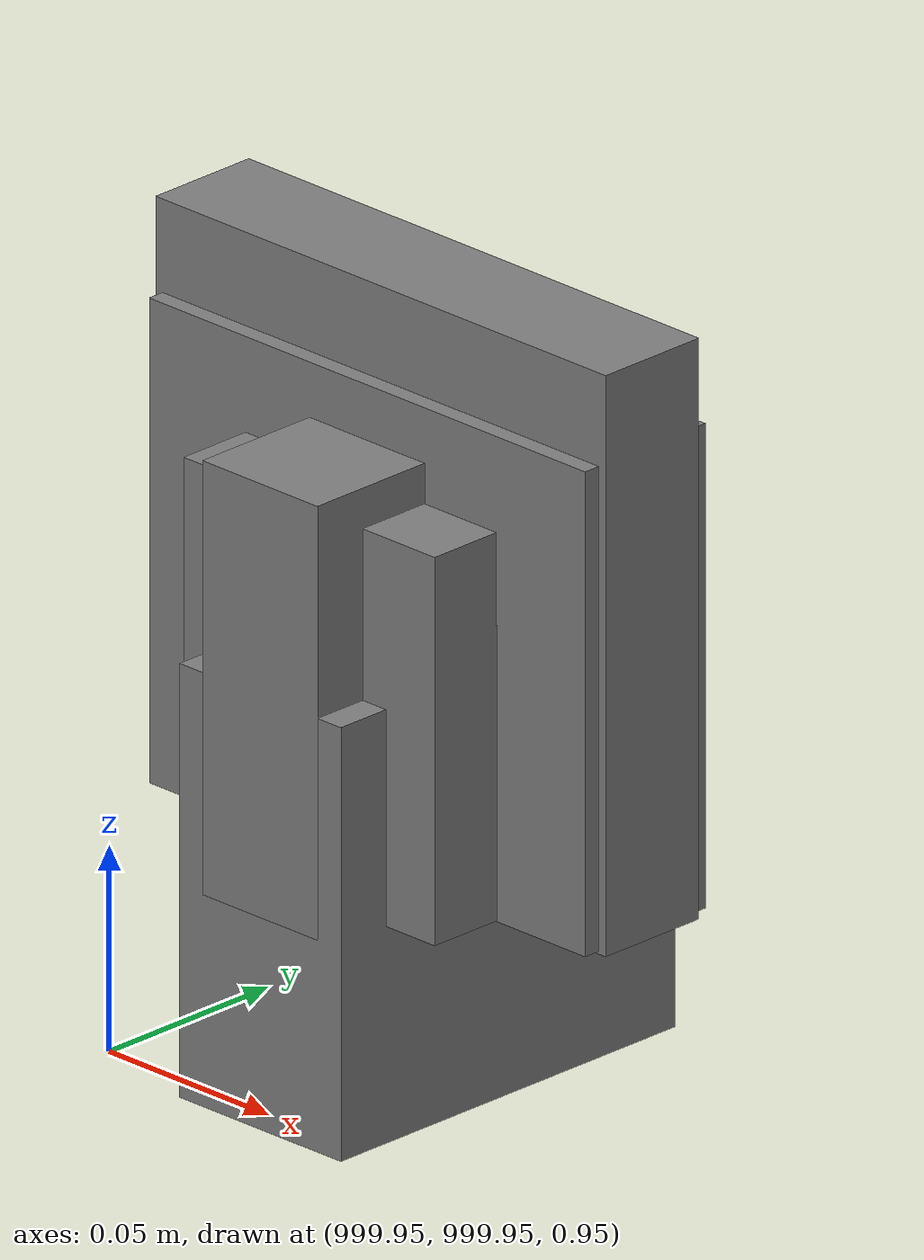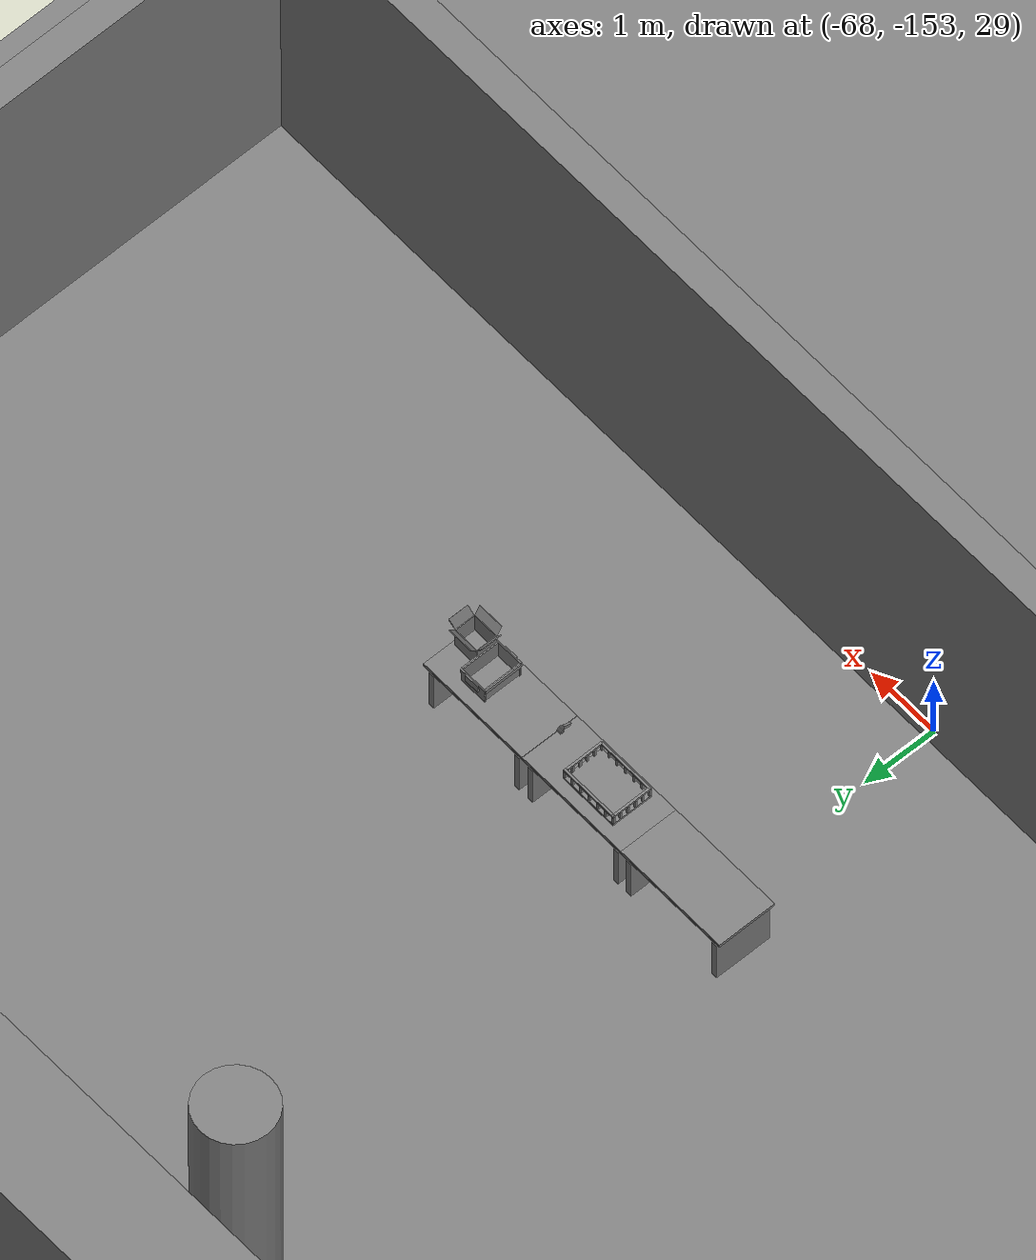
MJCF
<mujoco>
    <option gravity="0.000000000 0.000000000 -9.810000420" timestep="0.0049999999" integrator="implicitfast" density="1.225" viscosity="1.8000001e-05" noslip_iterations="10" iterations="100" sdf_iterations="50">
        <flag multiccd="disable"/>
    </option>
    <size memory="1000M"/>
    <compiler coordinate="local"/>
    <worldbody>
        <light cutoff="30" pos="0 1 1" dir="0 -1 -2"/>
        <light cutoff="30" pos="0 -1 1" dir="0 1 -2"/>
        <body pos="1000.000000000 1000.000000000 1.000000000" euler="0.000000000 0.000000000 180.000000000" name="openloong_gripper_2f85_fix_base_usda_cpu_fan">
            <geom contype="1" conaffinity="1" density="1000" type="box" material="" rgba="0.500000000 0.500000000 0.500000000 1.000000000" solimp="0.899999976 0.949999988 0.001000000" friction="1.000000000 0.005000000 0.000100000" solref="0.020000000 1.000000000" margin="0" condim="3" group="0" pos="0.000000000 0.000000000 0.070034981" quat="0.000000000 0.000000000 0.000000000 1.000000000" size="0.070700005 0.014699999 0.070700005" name="openloong_gripper_2f85_fix_base_usda_geom_A02FE0BA_BAB2_4887_AA4C_716AC12F8142"/>
            <freejoint name="openloong_gripper_2f85_fix_base_usda_cpu_fan_joint"/>
            <site size="0.005000000 0.005000000 0.005000000" rgba="0.500000000 0.500000000 0.500000000 1.000000000" pos="0.000000000 0.000000000 0.000000000" quat="0.999961913 0.008726535 0.000000000 0.000000000" group="0" type="sphere" name="openloong_gripper_2f85_fix_base_usda_cpu_fancsite"/>
        </body>
        <body pos="-66.351425171 -148.971908569 31.169212341" euler="65.392745972 -51.217906952 10.377384186" mocap="true" name="spotlight3_SpotLight"/>
        <body pos="1000.000000000 1000.000000000 1.000000000" euler="0.000000000 0.000000000 180.000000000" name="openloong_gripper_2f85_fix_base_usda_wifi_box">
            <geom contype="1" conaffinity="1" density="1000" type="box" material="" rgba="0.500000000 0.500000000 0.500000000 1.000000000" solimp="0.899999976 0.949999988 0.001000000" friction="1.000000000 0.005000000 0.000100000" solref="0.020000000 1.000000000" margin="0" condim="3" group="0" pos="0.000000000 0.000000000 0.058978677" quat="0.000000000 0.000000047 0.000000000 1.000000000" size="0.068499997 0.018999999 0.059000000" name="openloong_gripper_2f85_fix_base_usda_geom_04446C2D_934D_4C04_982A_D6A137235EEE"/>
            <freejoint name="openloong_gripper_2f85_fix_base_usda_wifi_box_joint"/>
            <site size="0.005000000 0.005000000 0.005000000" rgba="0.500000000 0.500000000 0.500000000 1.000000000" pos="0.000000000 0.000000000 0.000000000" quat="0.999961913 0.008726500 0.000000000 0.000000000" group="0" type="sphere" name="openloong_gripper_2f85_fix_base_usda_wifi_boxsite"/>
        </body>
        <body pos="1000.000000000 1000.000000000 1.000000000" euler="0.000000000 0.000000000 180.000000000" name="openloong_gripper_2f85_fix_base_usda_battery_01">
            <geom contype="1" conaffinity="1" density="1000" type="box" material="" rgba="0.500000000 0.500000000 0.500000000 1.000000000" solimp="0.899999976 0.949999988 0.001000000" friction="1.000000000 0.005000000 0.000100000" solref="0.020000000 1.000000000" margin="0" condim="3" group="0" pos="-0.011123657 -0.041940309 0.101691343" quat="1.000000000 0.000000000 0.000000000 0.000000000" size="0.010800000 0.003375000 0.004725000" name="openloong_gripper_2f85_fix_base_usda_geom_30A74439_5A6C_4DD2_8AD6_26865FD9C8FF"/>
            <geom contype="1" conaffinity="1" density="1000" type="box" material="" rgba="0.500000000 0.500000000 0.500000000 1.000000000" solimp="0.899999976 0.949999988 0.001000000" friction="1.000000000 0.005000000 0.000100000" solref="0.020000000 1.000000000" margin="0" condim="3" group="0" pos="-0.010876465 -0.044247437 0.047066893" quat="0.998702705 -0.050920475 0.000000000 0.000000000" size="0.009450001 0.002700000 0.024975000" name="openloong_gripper_2f85_fix_base_usda_geom_4BB78BC7_7D39_4234_B487_78A8F3D1F841"/>
            <geom contype="1" conaffinity="1" density="1000" type="box" material="" rgba="0.500000000 0.500000000 0.500000000 1.000000000" solimp="0.899999976 0.949999988 0.001000000" friction="1.000000000 0.005000000 0.000100000" solref="0.020000000 1.000000000" margin="0" condim="3" group="0" pos="-0.001235962 -0.000659180 0.047381196" quat="1.000000000 0.000000000 0.000000000 0.000000000" size="0.039420001 0.039150000 0.047250003" name="openloong_gripper_2f85_fix_base_usda_geom_97A0C6FA_2BFE_4634_971A_A6DCB186997F"/>
            <geom contype="1" conaffinity="1" density="1000" type="box" material="" rgba="0.500000000 0.500000000 0.500000000 1.000000000" solimp="0.899999976 0.949999988 0.001000000" friction="1.000000000 0.005000000 0.000100000" solref="0.020000000 1.000000000" margin="0" condim="3" group="0" pos="-0.010876465 -0.039138794 0.009851727" quat="1.000000000 0.000000000 0.000000000 0.000000000" size="0.009450001 0.010800000 0.013500000" name="openloong_gripper_2f85_fix_base_usda_geom_9E2C0EA8_3DDF_4B23_8DDC_4D896DE1C562"/>
            <geom contype="1" conaffinity="1" density="1000" type="box" material="" rgba="0.500000000 0.500000000 0.500000000 1.000000000" solimp="0.899999976 0.949999988 0.001000000" friction="1.000000000 0.005000000 0.000100000" solref="0.020000000 1.000000000" margin="0" condim="3" group="0" pos="-0.010876465 -0.041528322 0.071508206" quat="1.000000000 0.000000000 0.000000000 0.000000000" size="0.009450001 0.002700000 0.027000001" name="openloong_gripper_2f85_fix_base_usda_geom_253E981C_ED9C_406D_AC29_BE34D57D87C9"/>
            <freejoint name="openloong_gripper_2f85_fix_base_usda_battery_01_joint"/>
            <site size="0.005000000 0.005000000 0.005000000" rgba="0.500000000 0.500000000 0.500000000 1.000000000" pos="0.000000000 0.000000000 0.000000000" quat="0.999961913 0.008726500 0.000000000 0.000000000" group="0" type="sphere" name="openloong_gripper_2f85_fix_base_usda_battery_01site"/>
        </body>
        <body pos="1000.000000000 1000.000000000 1.000000000" euler="0.000011953 0.000005123 -179.999984741" name="openloong_gripper_2f85_fix_base_usda_intel_box">
            <geom contype="1" conaffinity="1" density="1000" type="box" material="" rgba="0.500000000 0.500000000 0.500000000 1.000000000" solimp="0.899999976 0.949999988 0.001000000" friction="1.000000000 0.005000000 0.000100000" solref="0.020000000 1.000000000" margin="0" condim="3" group="0" pos="0.000000000 -0.000067139 0.000082284" quat="0.707106709 0.000000225 0.000000253 0.707106650" size="0.052800003 0.025300000 0.052800003" name="openloong_gripper_2f85_fix_base_usda_geom_22A16480_1328_4014_B621_B34E9CFA2288"/>
            <freejoint name="openloong_gripper_2f85_fix_base_usda_intel_box_joint"/>
            <site size="0.005000000 0.005000000 0.005000000" rgba="0.500000000 0.500000000 0.500000000 1.000000000" pos="0.000000000 0.000000000 0.000000000" quat="0.999961913 0.008726500 0.000000000 0.000000000" group="0" type="sphere" name="openloong_gripper_2f85_fix_base_usda_intel_boxsite"/>
        </body>
        <body pos="-66.115295410 -149.171157837 31.165513992" euler="-54.454925537 -57.549839020 -173.169921875" mocap="true" name="spotlight5_SpotLight"/>
        <body pos="1000.000000000 999.999938965 1.000000000" euler="0.000000000 0.000000000 180.000000000" name="openloong_gripper_2f85_fix_base_usda_intelcore_i5">
            <geom contype="1" conaffinity="1" density="1000" type="box" material="" rgba="0.500000000 0.500000000 0.500000000 1.000000000" solimp="0.899999976 0.949999988 0.001000000" friction="1.000000000 0.005000000 0.000100000" solref="0.020000000 1.000000000" margin="0" condim="3" group="0" pos="0.000000000 0.000000000 0.051722717" quat="0.707106709 0.000000000 0.000000000 -0.707106769" size="0.052800000 0.018080002 0.052800000" name="openloong_gripper_2f85_fix_base_usda_geom_57127041_2983_4643_BE34_4922B47A8F92"/>
            <freejoint name="openloong_gripper_2f85_fix_base_usda_intelcore_i5_joint"/>
            <site size="0.005000000 0.005000000 0.005000000" rgba="0.500000000 0.500000000 0.500000000 1.000000000" pos="0.000000000 0.000000000 0.000000000" quat="0.999961913 0.008726534 0.000000000 0.000000000" group="0" type="sphere" name="openloong_gripper_2f85_fix_base_usda_intelcore_i5site"/>
        </body>
        <body pos="-66.237884521 -149.523956299 31.165388107" euler="-66.995986938 -73.346214294 37.050022125" mocap="true" name="spotlight4_SpotLight"/>
        <body pos="-64.866622925 -149.383972168 30.183746338" euler="89.999984741 89.999946594 0.000000000" name="openloong_gripper_2f85_fix_base_usda_bluebox_01">
            <geom contype="1" conaffinity="1" density="1000" type="box" material="" rgba="0.500000000 0.500000000 0.500000000 1.000000000" solimp="0.899999976 0.949999988 0.001000000" friction="1.000000000 0.005000000 0.000100000" solref="0.020000000 1.000000000" margin="0" condim="3" group="0" pos="0.276580811 0.187225342 0.000068665" quat="0.707106948 0.000077471 0.707106352 0.000077486" size="0.100000001 0.057999998 0.010000000" name="openloong_gripper_2f85_fix_base_usda_geom_2C785ABE_58A3_47A4_82E0_D47E2461768A"/>
            <geom contype="1" conaffinity="1" density="1000" type="box" material="" rgba="0.500000000 0.500000000 0.500000000 1.000000000" solimp="0.899999976 0.949999988 0.001000000" friction="1.000000000 0.005000000 0.000100000" solref="0.020000000 1.000000000" margin="0" condim="3" group="0" pos="0.000000000 0.002883911 0.000000000" quat="0.999999881 0.000000000 0.000000000 0.000000000" size="0.254000008 0.003000000 0.172000006" name="openloong_gripper_2f85_fix_base_usda_geom_9068CC88_4524_4F6B_8F55_2D646793509A"/>
            <geom contype="1" conaffinity="1" density="1000" type="box" material="" rgba="0.500000000 0.500000000 0.500000000 1.000000000" solimp="0.899999976 0.949999988 0.001000000" friction="1.000000000 0.005000000 0.000100000" solref="0.020000000 1.000000000" margin="0" condim="3" group="0" pos="0.000000000 0.124874115 0.173484802" quat="0.999796331 0.020176515 -0.000000015 0.000000030" size="0.259999990 0.119999997 0.007000000" name="openloong_gripper_2f85_fix_base_usda_geom_7AC593AE_901E_4892_A63B_1D1B76F18D48"/>
            <geom contype="1" conaffinity="1" density="1000" type="box" material="" rgba="0.500000000 0.500000000 0.500000000 1.000000000" solimp="0.899999976 0.949999988 0.001000000" friction="1.000000000 0.005000000 0.000100000" solref="0.020000000 1.000000000" margin="0" condim="3" group="0" pos="0.000000000 0.124874115 -0.173469543" quat="0.999796331 -0.020176545 -0.000000015 0.000000000" size="0.259999990 0.119999997 0.007000000" name="openloong_gripper_2f85_fix_base_usda_geom_EEB89120_A6BB_4BAE_AF49_F3A285C03538"/>
            <geom contype="1" conaffinity="1" density="1000" type="box" material="" rgba="0.500000000 0.500000000 0.500000000 1.000000000" solimp="0.899999976 0.949999988 0.001000000" friction="1.000000000 0.005000000 0.000100000" solref="0.020000000 1.000000000" margin="0" condim="3" group="0" pos="0.000000000 0.214008331 0.188980103" quat="0.999912977 0.013176724 0.000000015 0.000000000" size="0.259999990 0.029999999 0.012500000" name="openloong_gripper_2f85_fix_base_usda_geom_03A393E3_2468_49A7_87B8_DF6F5E30E715"/>
            <geom contype="1" conaffinity="1" density="1000" type="box" material="" rgba="0.500000000 0.500000000 0.500000000 1.000000000" solimp="0.899999976 0.949999988 0.001000000" friction="1.000000000 0.005000000 0.000100000" solref="0.020000000 1.000000000" margin="0" condim="3" group="0" pos="-0.258361816 0.125289917 0.001876831" quat="0.702796936 -0.020792112 0.710783124 0.020769298" size="0.189999998 0.119999997 0.009000000" name="openloong_gripper_2f85_fix_base_usda_geom_A09BCFD8_8994_4546_ACD4_65162F5C3917"/>
            <geom contype="1" conaffinity="1" density="1000" type="box" material="" rgba="0.500000000 0.500000000 0.500000000 1.000000000" solimp="0.899999976 0.949999988 0.001000000" friction="1.000000000 0.005000000 0.000100000" solref="0.020000000 1.000000000" margin="0" condim="3" group="0" pos="0.000000000 0.214008331 -0.188980103" quat="0.999912977 -0.013176769 0.000000030 0.000000015" size="0.259999990 0.029999999 0.012500000" name="openloong_gripper_2f85_fix_base_usda_geom_A6A50914_21DA_4B5F_9F88_2AD9E2A444A9"/>
            <geom contype="1" conaffinity="1" density="1000" type="box" material="" rgba="0.500000000 0.500000000 0.500000000 1.000000000" solimp="0.899999976 0.949999988 0.001000000" friction="1.000000000 0.005000000 0.000100000" solref="0.020000000 1.000000000" margin="0" condim="3" group="0" pos="-0.276611328 0.187225342 0.000068665" quat="0.707106650 0.000077441 0.707106709 0.000077456" size="0.100000001 0.057999998 0.010000000" name="openloong_gripper_2f85_fix_base_usda_geom_8C645938_230A_4678_84CB_242218B14F8F"/>
            <geom contype="1" conaffinity="1" density="1000" type="box" material="" rgba="0.500000000 0.500000000 0.500000000 1.000000000" solimp="0.899999976 0.949999988 0.001000000" friction="1.000000000 0.005000000 0.000100000" solref="0.020000000 1.000000000" margin="0" condim="3" group="0" pos="0.258331299 0.125289917 0.001876831" quat="0.702851415 0.018856421 0.710823774 -0.019329369" size="0.189999998 0.119999997 0.009000000" name="openloong_gripper_2f85_fix_base_usda_geom_1BAB4BCF_8831_4E1D_BAF4_519241F357FF"/>
            <freejoint name="openloong_gripper_2f85_fix_base_usda_bluebox_01_joint"/>
            <site size="0.005000000 0.005000000 0.005000000" rgba="0.500000000 0.500000000 0.500000000 1.000000000" pos="0.000000000 0.000000000 0.000000000" quat="0.999961913 0.008726534 0.000000000 0.000000000" group="0" type="sphere" name="openloong_gripper_2f85_fix_base_usda_bluebox_01site"/>
        </body>
        <body pos="-64.496299744 -149.491867065 30.235729218" euler="0.000000000 0.000000000 89.999946594" name="openloong_gripper_2f85_fix_base_usda_cardboardbox_01">
            <geom contype="1" conaffinity="1" density="1000" type="box" material="" rgba="0.500000000 0.500000000 0.500000000 1.000000000" solimp="0.899999976 0.949999988 0.001000000" friction="1.000000000 0.005000000 0.000100000" solref="0.020000000 1.000000000" margin="0" condim="3" group="0" pos="-0.003166199 -0.004086494 0.005052090" quat="1.000000000 0.000000000 0.000000000 0.000000000" size="0.142499998 0.177500010 0.005000000" name="openloong_gripper_2f85_fix_base_usda_geom_C29C22F9_A884_4EC1_B5D7_3A61118CC5BD"/>
            <geom contype="1" conaffinity="1" density="1000" type="box" material="" rgba="0.500000000 0.500000000 0.500000000 1.000000000" solimp="0.899999976 0.949999988 0.001000000" friction="1.000000000 0.005000000 0.000100000" solref="0.020000000 1.000000000" margin="0" condim="3" group="0" pos="-0.003166199 0.170316696 0.150570869" quat="1.000000000 0.000000000 0.000000000 0.000000000" size="0.142499998 0.005000000 0.149999991" name="openloong_gripper_2f85_fix_base_usda_geom_BAEF6C1F_E0B7_4B12_880A_115C8D72DAE7"/>
            <geom contype="1" conaffinity="1" density="1000" type="box" material="" rgba="0.500000000 0.500000000 0.500000000 1.000000000" solimp="0.899999976 0.949999988 0.001000000" friction="1.000000000 0.005000000 0.000100000" solref="0.020000000 1.000000000" margin="0" condim="3" group="0" pos="-0.147399902 -0.005307198 0.150570869" quat="1.000000000 0.000000000 0.000000000 0.000000000" size="0.005000000 0.177500010 0.149999991" name="openloong_gripper_2f85_fix_base_usda_geom_B21114F8_7FAD_4958_80D0_7CEAB63D4923"/>
            <geom contype="1" conaffinity="1" density="1000" type="box" material="" rgba="0.500000000 0.500000000 0.500000000 1.000000000" solimp="0.899999976 0.949999988 0.001000000" friction="1.000000000 0.005000000 0.000100000" solref="0.020000000 1.000000000" margin="0" condim="3" group="0" pos="0.140275955 -0.005307198 0.150570869" quat="1.000000000 0.000000000 0.000000000 0.000000000" size="0.005000000 0.177500010 0.149999991" name="openloong_gripper_2f85_fix_base_usda_geom_1C3F82FC_14FF_46B3_B522_07727BBBC3AC"/>
            <geom contype="1" conaffinity="1" density="1000" type="box" material="" rgba="0.500000000 0.500000000 0.500000000 1.000000000" solimp="0.899999976 0.949999988 0.001000000" friction="1.000000000 0.005000000 0.000100000" solref="0.020000000 1.000000000" margin="0" condim="3" group="0" pos="-0.003166199 -0.181550980 0.150570869" quat="1.000000000 0.000000000 0.000000000 0.000000000" size="0.142499998 0.005000000 0.149999991" name="openloong_gripper_2f85_fix_base_usda_geom_09261DF8_0F4D_4432_9E98_CDA0B277F618"/>
            <freejoint name="openloong_gripper_2f85_fix_base_usda_cardboardbox_01_joint"/>
            <site size="0.005000000 0.005000000 0.005000000" rgba="0.500000000 0.500000000 0.500000000 1.000000000" pos="0.000000000 0.000000000 0.000000000" quat="0.999961913 0.008726535 0.000000000 0.000000000" group="0" type="sphere" name="openloong_gripper_2f85_fix_base_usda_site_7B42B651_E125_4B8F_91E7_323BC281D236"/>
            <body pos="0.139160156 -0.004048347 0.301930904" euler="-179.999954224 49.383502960 179.999954224" name="openloong_gripper_2f85_fix_base_usda_A1_006">
                <geom contype="1" conaffinity="1" density="1000" type="box" material="" rgba="0.500000000 0.500000000 0.500000000 1.000000000" solimp="0.899999976 0.949999988 0.001000000" friction="1.000000000 0.005000000 0.000100000" solref="0.020000000 1.000000000" margin="0" condim="3" group="0" pos="-0.071587563 0.000009537 0.001745224" quat="0.999999881 0.000000000 0.000000000 0.000000000" size="0.071249999 0.179999992 0.002500000" name="openloong_gripper_2f85_fix_base_usda_geom_9D94A59F_805C_4893_945E_F8DBCC1A8CFD"/>
                <joint armature="0" stiffness="0.07" damping="0.0099999998" axis="0.000000 1.000000 0.000000" type="hinge" name="openloong_gripper_2f85_fix_base_usda_A1_006"/>
            </body>
            <body pos="-0.145902634 -0.004086494 0.301938057" euler="-180.000000000 -60.000011444 -180.000000000" name="openloong_gripper_2f85_fix_base_usda_A2_006">
                <geom contype="1" conaffinity="1" density="1000" type="box" material="" rgba="0.500000000 0.500000000 0.500000000 1.000000000" solimp="0.899999976 0.949999988 0.001000000" friction="1.000000000 0.005000000 0.000100000" solref="0.020000000 1.000000000" margin="0" condim="3" group="0" pos="0.071268082 0.000009537 0.002717972" quat="0.000002921 0.000000000 -0.000000030 0.999999881" size="0.071249999 0.179999992 0.002500000" name="openloong_gripper_2f85_fix_base_usda_geom_8169532A_B3BF_4EAA_8294_B4C6222E5180"/>
                <joint armature="0" stiffness="0.07" damping="0.0099999998" axis="0.000000 1.000000 0.000000" type="hinge" name="openloong_gripper_2f85_fix_base_usda_A2_006"/>
            </body>
            <body pos="-0.003385544 0.175991058 0.301930904" euler="-125.858116150 -0.000004561 0.000002331" name="openloong_gripper_2f85_fix_base_usda_B2_006">
                <geom contype="1" conaffinity="1" density="1000" type="box" material="" rgba="0.500000000 0.500000000 0.500000000 1.000000000" solimp="0.899999976 0.949999988 0.001000000" friction="1.000000000 0.005000000 0.000100000" solref="0.020000000 1.000000000" margin="0" condim="3" group="0" pos="0.000009537 -0.070939064 -0.002470016" quat="0.999614120 0.027776197 -0.000000015 0.000000030" size="0.137500003 0.064999998 0.005000000" name="openloong_gripper_2f85_fix_base_usda_geom_A6531550_13E4_43D1_B889_E7D929A58AD1"/>
                <joint armature="0" stiffness="0.07" damping="0.0099999998" axis="1.000000 0.000000 0.000000" type="hinge" name="openloong_gripper_2f85_fix_base_usda_B2_006"/>
            </body>
            <body pos="-0.003385544 -0.184140205 0.301938057" euler="147.805557251 0.000000000 0.000000000" name="openloong_gripper_2f85_fix_base_usda_B1_006">
                <geom contype="1" conaffinity="1" density="1000" type="box" material="" rgba="0.500000000 0.500000000 0.500000000 1.000000000" solimp="0.899999976 0.949999988 0.001000000" friction="1.000000000 0.005000000 0.000100000" solref="0.020000000 1.000000000" margin="0" condim="3" group="0" pos="-0.000028610 0.070202351 -0.002703667" quat="0.999614179 -0.027776167 0.000000000 0.000000000" size="0.137500003 0.064999998 0.005000000" name="openloong_gripper_2f85_fix_base_usda_geom_D649B028_83B1_40DE_8C4B_6E6A5C6EB70E"/>
                <joint armature="0" stiffness="0.07" damping="0.0099999998" axis="1.000000 0.000000 0.000000" type="hinge" name="openloong_gripper_2f85_fix_base_usda_B1_006"/>
            </body>
        </body>
        <body pos="-65.882858276 -149.481979370 30.229999542" euler="-64.487716675 0.000000000 0.000000000" name="openloong_gripper_2f85_fix_base_usda_Barcode">
            <geom contype="1" conaffinity="1" density="1000" type="box" material="" rgba="0.500000000 0.500000000 0.500000000 1.000000000" solimp="0.899999976 0.949999988 0.001000000" friction="1.000000000 0.005000000 0.000100000" solref="0.020000000 1.000000000" margin="0" condim="3" group="0" pos="0.000000000 0.013038635 0.001419067" quat="0.000000000 0.000000000 0.000000000 1.000000119" size="0.034000002 0.010000000 0.017999999" name="openloong_gripper_2f85_fix_base_usda_geom_9CEDE5DB_C29F_4C4A_A0E0_E4D79F4A9C60"/>
            <geom contype="1" conaffinity="1" density="1000" type="box" material="" rgba="0.500000000 0.500000000 0.500000000 1.000000000" solimp="0.899999976 0.949999988 0.001000000" friction="1.000000000 0.005000000 0.000100000" solref="0.020000000 1.000000000" margin="0" condim="3" group="0" pos="0.000000000 -0.035301208 -0.007095337" quat="0.000000000 0.000000000 -0.043619365 0.999048233" size="0.028999999 0.010000000 0.020000000" name="openloong_gripper_2f85_fix_base_usda_geom_9BD7F604_B4AC_4745_95AF_AC80008845FE"/>
            <geom contype="1" conaffinity="1" density="1000" type="box" material="" rgba="0.500000000 0.500000000 0.500000000 1.000000000" solimp="0.899999976 0.949999988 0.001000000" friction="1.000000000 0.005000000 0.000100000" solref="0.020000000 1.000000000" margin="0" condim="3" group="0" pos="0.000000000 -0.043411255 -0.011749268" quat="0.922262907 0.386563420 0.000000000 0.000000000" size="0.026000001 0.010000000 0.020000000" name="openloong_gripper_2f85_fix_base_usda_geom_140675DB_7D8F_459A_91AC_FC45CC450A56"/>
            <geom contype="1" conaffinity="1" density="1000" type="box" material="" rgba="0.500000000 0.500000000 0.500000000 1.000000000" solimp="0.899999976 0.949999988 0.001000000" friction="1.000000000 0.005000000 0.000100000" solref="0.020000000 1.000000000" margin="0" condim="3" group="0" pos="0.000000000 -0.016967773 -0.031860352" quat="0.000000000 0.000000000 0.000000000 1.000000119" size="0.008000000 0.010000000 0.013000000" name="openloong_gripper_2f85_fix_base_usda_geom_2E9843A9_A744_4C9A_8D2D_A6DA83BF9DBC"/>
            <geom contype="1" conaffinity="1" density="1000" type="box" material="" rgba="0.500000000 0.500000000 0.500000000 1.000000000" solimp="0.899999976 0.949999988 0.001000000" friction="1.000000000 0.005000000 0.000100000" solref="0.020000000 1.000000000" margin="0" condim="3" group="0" pos="0.000000000 -0.001869202 0.000312805" quat="0.953716993 0.300705761 0.000000000 0.000000000" size="0.032000002 0.010000000 0.018999999" name="openloong_gripper_2f85_fix_base_usda_geom_F666385A_3602_490D_A150_2750678DE3C8"/>
            <geom contype="1" conaffinity="1" density="1000" type="box" material="" rgba="0.500000000 0.500000000 0.500000000 1.000000000" solimp="0.899999976 0.949999988 0.001000000" friction="1.000000000 0.005000000 0.000100000" solref="0.020000000 1.000000000" margin="0" condim="3" group="0" pos="0.000000000 -0.019531250 -0.003173828" quat="0.953716993 0.300705761 0.000000000 0.000000000" size="0.030999999 0.010000000 0.020000000" name="openloong_gripper_2f85_fix_base_usda_geom_847AC0F2_BC6C_4B98_BA71_7A9FC7C62ED2"/>
            <geom contype="1" conaffinity="1" density="1000" type="box" material="" rgba="0.500000000 0.500000000 0.500000000 1.000000000" solimp="0.899999976 0.949999988 0.001000000" friction="1.000000000 0.005000000 0.000100000" solref="0.020000000 1.000000000" margin="0" condim="3" group="0" pos="0.000000000 -0.035301208 -0.007095337" quat="0.953716993 0.300705761 0.000000000 0.000000000" size="0.028999999 0.010000000 0.020000000" name="openloong_gripper_2f85_fix_base_usda_geom_63BEE0F1_F6CA_4BE6_8B88_3AFE83EFCD91"/>
            <geom contype="1" conaffinity="1" density="1000" type="box" material="" rgba="0.500000000 0.500000000 0.500000000 1.000000000" solimp="0.899999976 0.949999988 0.001000000" friction="1.000000000 0.005000000 0.000100000" solref="0.020000000 1.000000000" margin="0" condim="3" group="0" pos="0.000000000 -0.042617798 -0.071121216" quat="0.000000000 0.000000000 0.000000000 1.000000119" size="0.013000000 0.021000000 0.059999999" name="openloong_gripper_2f85_fix_base_usda_geom_78DBBE28_4D20_4E1D_BFDB_B0DBF4378889"/>
            <freejoint name="openloong_gripper_2f85_fix_base_usda_Barcode_joint"/>
            <site size="0.005000000 0.005000000 0.005000000" rgba="0.500000000 0.500000000 0.500000000 1.000000000" pos="0.000000000 0.000000000 0.000000000" quat="1.000000000 0.000000000 0.000000000 0.000000000" group="0" type="sphere" name="openloong_gripper_2f85_fix_base_usda_Barcode_site"/>
        </body>
        <body pos="-66.745018005 -149.392349243 30.184000015" euler="0.000000000 0.000000000 89.999946594" name="[22333339664005]_Basket_01">
            <geom contype="1" conaffinity="1" density="1000" type="box" material="" rgba="0.500000000 0.500000000 0.500000000 1.000000000" solimp="0.899999976 0.949999988 0.001000000" friction="1.000000000 0.005000000 0.000100000" solref="0.020000000 1.000000000" margin="0" condim="3" group="0" pos="-0.052425385 0.389207840 0.089787483" quat="0.707107008 0.000000000 0.000000000 0.707106411" size="0.014249999 0.014249999 0.059999999" name="[22333339664005]_geom_8C4C7C58_ACB5_4536_A3CD_D225D6F31967"/>
            <geom contype="1" conaffinity="1" density="1000" type="box" material="" rgba="0.500000000 0.500000000 0.500000000 1.000000000" solimp="0.899999976 0.949999988 0.001000000" friction="1.000000000 0.005000000 0.000100000" solref="0.020000000 1.000000000" margin="0" condim="3" group="0" pos="0.264015198 -0.133043289 0.089787483" quat="0.707107008 0.000000000 0.000000000 0.707106411" size="0.014249999 0.014249999 0.059999999" name="[22333339664005]_geom_5EA56EF1_8FA6_4B47_B8F3_F7C04BF06495"/>
            <geom contype="1" conaffinity="1" density="1000" type="box" material="" rgba="0.500000000 0.500000000 0.500000000 1.000000000" solimp="0.899999976 0.949999988 0.001000000" friction="1.000000000 0.005000000 0.000100000" solref="0.020000000 1.000000000" margin="0" condim="3" group="0" pos="-0.264015198 -0.265548706 0.089793205" quat="0.707107008 0.000000000 0.000000000 0.707106411" size="0.014249999 0.014249999 0.059999999" name="[22333339664005]_geom_82340BDE_509B_46A8_9389_27D4F49D8275"/>
            <geom contype="1" conaffinity="1" density="1000" type="box" material="" rgba="0.500000000 0.500000000 0.500000000 1.000000000" solimp="0.899999976 0.949999988 0.001000000" friction="1.000000000 0.005000000 0.000100000" solref="0.020000000 1.000000000" margin="0" condim="3" group="0" pos="-0.160263062 -0.389322281 0.089793205" quat="0.707107008 0.000000000 0.000000000 0.707106411" size="0.014249999 0.014249999 0.059999999" name="[22333339664005]_geom_7D11F749_94B9_479D_96D5_FACB665DB25E"/>
            <geom contype="1" conaffinity="1" density="1000" type="box" material="" rgba="0.500000000 0.500000000 0.500000000 1.000000000" solimp="0.899999976 0.949999988 0.001000000" friction="1.000000000 0.005000000 0.000100000" solref="0.020000000 1.000000000" margin="0" condim="3" group="0" pos="0.162265778 -0.389322281 0.089787483" quat="0.707107008 0.000000000 0.000000000 0.707106411" size="0.014249999 0.014249999 0.059999999" name="[22333339664005]_geom_3270DB44_CFE4_4B5E_AF72_7C58F4D1B5C7"/>
            <geom contype="1" conaffinity="1" density="1000" type="box" material="" rgba="0.500000000 0.500000000 0.500000000 1.000000000" solimp="0.899999976 0.949999988 0.001000000" friction="1.000000000 0.005000000 0.000100000" solref="0.020000000 1.000000000" margin="0" condim="3" group="0" pos="0.264015198 0.389207840 0.089787483" quat="0.707107008 0.000000000 0.000000000 0.707106411" size="0.014249999 0.014249999 0.059999999" name="[22333339664005]_geom_50CA3492_99BC_4B7A_9D8E_BD9D03F5D496"/>
            <geom contype="1" conaffinity="1" density="1000" type="box" material="" rgba="0.500000000 0.500000000 0.500000000 1.000000000" solimp="0.899999976 0.949999988 0.001000000" friction="1.000000000 0.005000000 0.000100000" solref="0.020000000 1.000000000" margin="0" condim="3" group="0" pos="-0.264015198 -0.133043289 0.089793205" quat="0.707107008 0.000000000 0.000000000 0.707106411" size="0.014249999 0.014249999 0.059999999" name="[22333339664005]_geom_5918F6F4_56FB_4FB3_B3B3_B23C42A69EE4"/>
            <geom contype="1" conaffinity="1" density="1000" type="box" material="" rgba="0.500000000 0.500000000 0.500000000 1.000000000" solimp="0.899999976 0.949999988 0.001000000" friction="1.000000000 0.005000000 0.000100000" solref="0.020000000 1.000000000" margin="0" condim="3" group="0" pos="-0.264026642 0.269256592 0.089793205" quat="0.707107008 0.000000000 0.000000000 0.707106411" size="0.014249999 0.014249999 0.059999999" name="[22333339664005]_geom_8A032678_F26E_43A2_A97C_F47A872BC04A"/>
            <geom contype="1" conaffinity="1" density="1000" type="box" material="" rgba="0.500000000 0.500000000 0.500000000 1.000000000" solimp="0.899999976 0.949999988 0.001000000" friction="1.000000000 0.005000000 0.000100000" solref="0.020000000 1.000000000" margin="0" condim="3" group="0" pos="0.054462433 0.389207840 0.089787483" quat="0.707107008 0.000000000 0.000000000 0.707106411" size="0.014249999 0.014249999 0.059999999" name="[22333339664005]_geom_F7418EAB_31C2_43B2_9247_FD59B96D02B4"/>
            <geom contype="1" conaffinity="1" density="1000" type="box" material="" rgba="0.500000000 0.500000000 0.500000000 1.000000000" solimp="0.899999976 0.949999988 0.001000000" friction="1.000000000 0.005000000 0.000100000" solref="0.020000000 1.000000000" margin="0" condim="3" group="0" pos="0.054462433 -0.389322281 0.089787483" quat="0.707107008 0.000000000 0.000000000 0.707106411" size="0.014249999 0.014249999 0.059999999" name="[22333339664005]_geom_B88EA110_BFA3_4EBF_BA09_F8B2C08FAF9B"/>
            <geom contype="1" conaffinity="1" density="1000" type="box" material="" rgba="0.500000000 0.500000000 0.500000000 1.000000000" solimp="0.899999976 0.949999988 0.001000000" friction="1.000000000 0.005000000 0.000100000" solref="0.020000000 1.000000000" margin="0" condim="3" group="0" pos="0.264015198 0.269256592 0.089793205" quat="0.707107008 0.000000000 0.000000000 0.707106411" size="0.014249999 0.014249999 0.059999999" name="[22333339664005]_geom_508DD1A4_4355_48DF_B230_1EBF7FFC28DC"/>
            <geom contype="1" conaffinity="1" density="1000" type="box" material="" rgba="0.500000000 0.500000000 0.500000000 1.000000000" solimp="0.899999976 0.949999988 0.001000000" friction="1.000000000 0.005000000 0.000100000" solref="0.020000000 1.000000000" margin="0" condim="3" group="0" pos="0.264015198 -0.389322281 0.089787483" quat="0.707107008 0.000000000 0.000000000 0.707106411" size="0.014249999 0.014249999 0.059999999" name="[22333339664005]_geom_94FACFEC_FBAE_4FC6_8D7C_9DEFDF0BDD1F"/>
            <geom contype="1" conaffinity="1" density="1000" type="box" material="" rgba="0.500000000 0.500000000 0.500000000 1.000000000" solimp="0.899999976 0.949999988 0.001000000" friction="1.000000000 0.005000000 0.000100000" solref="0.020000000 1.000000000" margin="0" condim="3" group="0" pos="0.000000000 0.000000000 0.015998840" quat="0.707107008 0.000000000 0.000000000 0.707106411" size="0.403499991 0.279000014 0.015750000" name="[22333339664005]_geom_5911C26B_C891_4C18_9495_6FFEF09B8E3E"/>
            <geom contype="1" conaffinity="1" density="1000" type="box" material="" rgba="0.500000000 0.500000000 0.500000000 1.000000000" solimp="0.899999976 0.949999988 0.001000000" friction="1.000000000 0.005000000 0.000100000" solref="0.020000000 1.000000000" margin="0" condim="3" group="0" pos="0.000000000 -0.389476776 0.163619041" quat="0.707107008 0.000000000 0.000000000 0.707106411" size="0.015000000 0.277500004 0.015750000" name="[22333339664005]_geom_3CD7882E_BB12_45FB_9D9A_8E8794EA7CEA"/>
            <geom contype="1" conaffinity="1" density="1000" type="box" material="" rgba="0.500000000 0.500000000 0.500000000 1.000000000" solimp="0.899999976 0.949999988 0.001000000" friction="1.000000000 0.005000000 0.000100000" solref="0.020000000 1.000000000" margin="0" condim="3" group="0" pos="0.162265778 0.389207840 0.089787483" quat="0.707107008 0.000000000 0.000000000 0.707106411" size="0.014249999 0.014249999 0.059999999" name="[22333339664005]_geom_A13FED50_FA36_4F48_9DDA_81DD5294842E"/>
            <geom contype="1" conaffinity="1" density="1000" type="box" material="" rgba="0.500000000 0.500000000 0.500000000 1.000000000" solimp="0.899999976 0.949999988 0.001000000" friction="1.000000000 0.005000000 0.000100000" solref="0.020000000 1.000000000" margin="0" condim="3" group="0" pos="0.000000000 0.389471054 0.163619041" quat="0.707107008 0.000000000 0.000000000 0.707106411" size="0.015000000 0.277500004 0.015750000" name="[22333339664005]_geom_F7D5254B_8127_40EC_B15B_C099D3C071DE"/>
            <geom contype="1" conaffinity="1" density="1000" type="box" material="" rgba="0.500000000 0.500000000 0.500000000 1.000000000" solimp="0.899999976 0.949999988 0.001000000" friction="1.000000000 0.005000000 0.000100000" solref="0.020000000 1.000000000" margin="0" condim="3" group="0" pos="-0.263511658 0.000000000 0.163619041" quat="0.707107008 0.000000000 0.000000000 0.707106411" size="0.403499991 0.015000000 0.015750000" name="[22333339664005]_geom_E515BF8F_B9D2_4840_A16D_B623BAA6DB37"/>
            <geom contype="1" conaffinity="1" density="1000" type="box" material="" rgba="0.500000000 0.500000000 0.500000000 1.000000000" solimp="0.899999976 0.949999988 0.001000000" friction="1.000000000 0.005000000 0.000100000" solref="0.020000000 1.000000000" margin="0" condim="3" group="0" pos="-0.264015198 0.141334534 0.089793205" quat="0.707107008 0.000000000 0.000000000 0.707106411" size="0.014249999 0.014249999 0.059999999" name="[22333339664005]_geom_DF895FB5_61AB_46C4_BE3B_C897AEFC380E"/>
            <geom contype="1" conaffinity="1" density="1000" type="box" material="" rgba="0.500000000 0.500000000 0.500000000 1.000000000" solimp="0.899999976 0.949999988 0.001000000" friction="1.000000000 0.005000000 0.000100000" solref="0.020000000 1.000000000" margin="0" condim="3" group="0" pos="0.264015198 -0.265548706 0.089787483" quat="0.707107008 0.000000000 0.000000000 0.707106411" size="0.014249999 0.014249999 0.059999999" name="[22333339664005]_geom_F3956A04_A550_4027_A05A_60EFA65FD67B"/>
            <geom contype="1" conaffinity="1" density="1000" type="box" material="" rgba="0.500000000 0.500000000 0.500000000 1.000000000" solimp="0.899999976 0.949999988 0.001000000" friction="1.000000000 0.005000000 0.000100000" solref="0.020000000 1.000000000" margin="0" condim="3" group="0" pos="-0.160263062 0.389207840 0.089787483" quat="0.707107008 0.000000000 0.000000000 0.707106411" size="0.014249999 0.014249999 0.059999999" name="[22333339664005]_geom_973403B1_6B44_426F_BCBA_28E4B731D2FC"/>
            <geom contype="1" conaffinity="1" density="1000" type="box" material="" rgba="0.500000000 0.500000000 0.500000000 1.000000000" solimp="0.899999976 0.949999988 0.001000000" friction="1.000000000 0.005000000 0.000100000" solref="0.020000000 1.000000000" margin="0" condim="3" group="0" pos="-0.052425385 -0.389322281 0.089787483" quat="0.707107008 0.000000000 0.000000000 0.707106411" size="0.014249999 0.014249999 0.059999999" name="[22333339664005]_geom_CEC76112_DA60_40B4_B4BA_6E3598D0E261"/>
            <geom contype="1" conaffinity="1" density="1000" type="box" material="" rgba="0.500000000 0.500000000 0.500000000 1.000000000" solimp="0.899999976 0.949999988 0.001000000" friction="1.000000000 0.005000000 0.000100000" solref="0.020000000 1.000000000" margin="0" condim="3" group="0" pos="-0.264026642 -0.389322281 0.089793205" quat="0.707107008 0.000000000 0.000000000 0.707106411" size="0.014249999 0.014249999 0.059999999" name="[22333339664005]_geom_997A38FB_CB17_4D3C_AD53_F9AD0DF745D0"/>
            <geom contype="1" conaffinity="1" density="1000" type="box" material="" rgba="0.500000000 0.500000000 0.500000000 1.000000000" solimp="0.899999976 0.949999988 0.001000000" friction="1.000000000 0.005000000 0.000100000" solref="0.020000000 1.000000000" margin="0" condim="3" group="0" pos="0.264015198 0.141334534 0.089787483" quat="0.707107008 0.000000000 0.000000000 0.707106411" size="0.014249999 0.014249999 0.059999999" name="[22333339664005]_geom_E852DE67_3E76_4D2A_BD01_6DFECF96BE1C"/>
            <geom contype="1" conaffinity="1" density="1000" type="box" material="" rgba="0.500000000 0.500000000 0.500000000 1.000000000" solimp="0.899999976 0.949999988 0.001000000" friction="1.000000000 0.005000000 0.000100000" solref="0.020000000 1.000000000" margin="0" condim="3" group="0" pos="-0.264015198 0.389207840 0.089793205" quat="0.707107008 0.000000000 0.000000000 0.707106411" size="0.014249999 0.014249999 0.059999999" name="[22333339664005]_geom_1EDEA330_8403_4E7E_B05D_0023DF0D9890"/>
            <geom contype="1" conaffinity="1" density="1000" type="box" material="" rgba="0.500000000 0.500000000 0.500000000 1.000000000" solimp="0.899999976 0.949999988 0.001000000" friction="1.000000000 0.005000000 0.000100000" solref="0.020000000 1.000000000" margin="0" condim="3" group="0" pos="0.264015198 0.004480362 0.089787483" quat="0.707107008 0.000000000 0.000000000 0.707106411" size="0.014249999 0.014249999 0.059999999" name="[22333339664005]_geom_55B040F8_FD45_49A3_8485_445CF345B2C7"/>
            <geom contype="1" conaffinity="1" density="1000" type="box" material="" rgba="0.500000000 0.500000000 0.500000000 1.000000000" solimp="0.899999976 0.949999988 0.001000000" friction="1.000000000 0.005000000 0.000100000" solref="0.020000000 1.000000000" margin="0" condim="3" group="0" pos="0.263694763 -0.000011444 0.163619041" quat="0.707107008 0.000000000 0.000000000 0.707106411" size="0.403499991 0.015000000 0.015750000" name="[22333339664005]_geom_ADFED5AD_623A_425A_93B0_C26DFF86DD6E"/>
            <geom contype="1" conaffinity="1" density="1000" type="box" material="" rgba="0.500000000 0.500000000 0.500000000 1.000000000" solimp="0.899999976 0.949999988 0.001000000" friction="1.000000000 0.005000000 0.000100000" solref="0.020000000 1.000000000" margin="0" condim="3" group="0" pos="-0.264015198 0.004480362 0.089793205" quat="0.707107008 0.000000000 0.000000000 0.707106411" size="0.014249999 0.014249999 0.059999999" name="[22333339664005]_geom_A50B19F9_1308_4BE3_924C_F5C48F56436E"/>
            <freejoint name="[22333339664005]_joint_68F8DC81_4ADE_42F6_B50A_58E7A17376C0"/>
        </body>
        <body pos="0.000000000 0.000000000 0.000000000" euler="0.000000000 0.000000000 0.000000000" name="Static Objects_Static Objects">
            <geom contype="1" conaffinity="1" density="1000" type="box" material="" rgba="0.500000000 0.500000000 0.500000000 1.000000000" solimp="0.899999976 0.949999988 0.001000000" friction="1.000000000 0.005000000 0.000100000" solref="0.020000000 1.000000000" margin="0" condim="3" group="0" pos="-67.544113159 -149.365814209 29.727830887" quat="0.500000417 0.499999970 0.499999553 0.499999970" size="0.381000012 0.319999993 0.041000001" name="Static Objects_geom_057CBFA0_5DAE_44B6_831B_A002F1143DBD"/>
            <geom contype="1" conaffinity="1" density="1000" type="box" material="" rgba="0.500000000 0.500000000 0.500000000 1.000000000" solimp="0.899999976 0.949999988 0.001000000" friction="1.000000000 0.005000000 0.000100000" solref="0.020000000 1.000000000" margin="0" condim="3" group="0" pos="-68.239501953 -149.365814209 30.086868286" quat="0.500000417 0.499999970 0.499999553 0.499999970" size="0.370999992 0.039500002 0.745000005" name="Static Objects_geom_F24D1709_3039_457B_921E_5FA67861D926"/>
            <geom contype="1" conaffinity="1" density="1000" type="box" material="" rgba="0.500000000 0.500000000 0.500000000 1.000000000" solimp="0.899999976 0.949999988 0.001000000" friction="1.000000000 0.005000000 0.000100000" solref="0.020000000 1.000000000" margin="0" condim="3" group="0" pos="-68.239501953 -149.365814209 30.147235870" quat="0.500000417 0.499999970 0.499999553 0.499999970" size="0.400000006 0.022000000 0.800000012" name="Static Objects_geom_02AEE70A_2CDE_49ED_ACCC_EADF0FA8E15B"/>
            <geom contype="1" conaffinity="1" density="1000" type="box" material="" rgba="0.500000000 0.500000000 0.500000000 1.000000000" solimp="0.899999976 0.949999988 0.001000000" friction="1.000000000 0.005000000 0.000100000" solref="0.020000000 1.000000000" margin="0" condim="3" group="0" pos="-68.934890747 -149.365814209 29.727830887" quat="0.500000417 0.499999970 0.499999553 0.499999970" size="0.381000012 0.319999993 0.041000001" name="Static Objects_geom_3292A08B_BC8A_4645_B6D9_E9937658B7C1"/>
            <geom contype="1" conaffinity="1" density="1000" type="box" material="" rgba="0.500000000 0.500000000 0.500000000 1.000000000" solimp="0.899999976 0.949999988 0.001000000" friction="1.000000000 0.005000000 0.000100000" solref="0.020000000 1.000000000" margin="0" condim="3" group="0" pos="-68.239501953 -149.365814209 29.561563492" quat="0.500000417 0.499999970 0.499999553 0.499999970" size="0.020000000 0.022000000 0.660000026" name="Static Objects_geom_7F0815A5_71C4_49E7_8F8C_27B15C44AAE7"/>
            <geom contype="1" conaffinity="1" density="1000" type="box" material="" rgba="0.500000000 0.500000000 0.500000000 1.000000000" solimp="0.899999976 0.949999988 0.001000000" friction="1.000000000 0.005000000 0.000100000" solref="0.020000000 1.000000000" margin="0" condim="3" group="0" pos="-65.945671082 -149.365814209 29.727830887" quat="0.500000417 0.499999970 0.499999553 0.499999970" size="0.381000012 0.319999993 0.041000001" name="Static Objects_geom_241ABE3D_6585_4914_9EE9_685622189C77"/>
            <geom contype="1" conaffinity="1" density="1000" type="box" material="" rgba="0.500000000 0.500000000 0.500000000 1.000000000" solimp="0.899999976 0.949999988 0.001000000" friction="1.000000000 0.005000000 0.000100000" solref="0.020000000 1.000000000" margin="0" condim="3" group="0" pos="-66.641059875 -149.365814209 30.086868286" quat="0.500000417 0.499999970 0.499999553 0.499999970" size="0.370999992 0.039500002 0.745000005" name="Static Objects_geom_76ABC101_0D39_4AFA_9029_0C982AE19AFD"/>
            <geom contype="1" conaffinity="1" density="1000" type="box" material="" rgba="0.500000000 0.500000000 0.500000000 1.000000000" solimp="0.899999976 0.949999988 0.001000000" friction="1.000000000 0.005000000 0.000100000" solref="0.020000000 1.000000000" margin="0" condim="3" group="0" pos="-66.641059875 -149.365814209 30.147235870" quat="0.500000417 0.499999970 0.499999553 0.499999970" size="0.400000006 0.022000000 0.800000012" name="Static Objects_geom_B171985B_AB8E_4E5F_993E_3B0420A4D3EF"/>
            <geom contype="1" conaffinity="1" density="1000" type="box" material="" rgba="0.500000000 0.500000000 0.500000000 1.000000000" solimp="0.899999976 0.949999988 0.001000000" friction="1.000000000 0.005000000 0.000100000" solref="0.020000000 1.000000000" margin="0" condim="3" group="0" pos="-67.336448669 -149.365814209 29.727830887" quat="0.500000417 0.499999970 0.499999553 0.499999970" size="0.381000012 0.319999993 0.041000001" name="Static Objects_geom_70C465A9_442F_4C6F_82E8_4F961BEC44B4"/>
            <geom contype="1" conaffinity="1" density="1000" type="box" material="" rgba="0.500000000 0.500000000 0.500000000 1.000000000" solimp="0.899999976 0.949999988 0.001000000" friction="1.000000000 0.005000000 0.000100000" solref="0.020000000 1.000000000" margin="0" condim="3" group="0" pos="-66.641059875 -149.365814209 29.561563492" quat="0.500000417 0.499999970 0.499999553 0.499999970" size="0.020000000 0.022000000 0.660000026" name="Static Objects_geom_6B0DAB6A_0779_407D_9623_642C5ADA6E36"/>
            <geom contype="1" conaffinity="1" density="1000" type="box" material="" rgba="0.500000000 0.500000000 0.500000000 1.000000000" solimp="0.899999976 0.949999988 0.001000000" friction="1.000000000 0.005000000 0.000100000" solref="0.020000000 1.000000000" margin="0" condim="3" group="0" pos="-64.338577271 -149.365814209 29.727830887" quat="0.500000417 0.499999970 0.499999553 0.499999970" size="0.381000012 0.319999993 0.041000001" name="Static Objects_geom_78CC5190_7E86_4C89_A2C2_9A8A3EE3D18E"/>
            <geom contype="1" conaffinity="1" density="1000" type="box" material="" rgba="0.500000000 0.500000000 0.500000000 1.000000000" solimp="0.899999976 0.949999988 0.001000000" friction="1.000000000 0.005000000 0.000100000" solref="0.020000000 1.000000000" margin="0" condim="3" group="0" pos="-65.033966064 -149.365814209 30.086868286" quat="0.500000417 0.499999970 0.499999553 0.499999970" size="0.370999992 0.039500002 0.745000005" name="Static Objects_geom_5A6D2260_1B2D_43EC_A6AA_C6B733C4DB9A"/>
            <geom contype="1" conaffinity="1" density="1000" type="box" material="" rgba="0.500000000 0.500000000 0.500000000 1.000000000" solimp="0.899999976 0.949999988 0.001000000" friction="1.000000000 0.005000000 0.000100000" solref="0.020000000 1.000000000" margin="0" condim="3" group="0" pos="-65.033966064 -149.365814209 30.147235870" quat="0.500000417 0.499999970 0.499999553 0.499999970" size="0.400000006 0.022000000 0.800000012" name="Static Objects_geom_415EF981_A71F_43AB_BE32_69E0ED1480EF"/>
            <geom contype="1" conaffinity="1" density="1000" type="box" material="" rgba="0.500000000 0.500000000 0.500000000 1.000000000" solimp="0.899999976 0.949999988 0.001000000" friction="1.000000000 0.005000000 0.000100000" solref="0.020000000 1.000000000" margin="0" condim="3" group="0" pos="-65.729354858 -149.365814209 29.727830887" quat="0.500000417 0.499999970 0.499999553 0.499999970" size="0.381000012 0.319999993 0.041000001" name="Static Objects_geom_9F58FD4E_5F91_48D6_B41B_AD2E46F2B481"/>
            <geom contype="1" conaffinity="1" density="1000" type="box" material="" rgba="0.500000000 0.500000000 0.500000000 1.000000000" solimp="0.899999976 0.949999988 0.001000000" friction="1.000000000 0.005000000 0.000100000" solref="0.020000000 1.000000000" margin="0" condim="3" group="0" pos="-65.033966064 -149.365814209 29.561563492" quat="0.500000417 0.499999970 0.499999553 0.499999970" size="0.020000000 0.022000000 0.660000026" name="Static Objects_geom_CBE5C9F5_FB0A_45F4_8A29_AC1C0F0F6733"/>
            <geom contype="1" conaffinity="1" density="1000" type="box" material="" rgba="0.500000000 0.500000000 0.500000000 1.000000000" solimp="0.899999976 0.949999988 0.001000000" friction="1.000000000 0.005000000 0.000100000" solref="0.020000000 1.000000000" margin="0" condim="3" group="0" pos="-61.754566193 -137.853729248 33.906845093" quat="0.707107067 0.000000000 0.000000000 0.707106471" size="0.759999990 0.759999990 4.500000000" name="Static Objects_geom_FD87935D_0569_4C8E_9F36_00E3F2BF505E"/>
            <geom contype="1" conaffinity="1" density="1000" type="box" material="" rgba="0.500000000 0.500000000 0.500000000 1.000000000" solimp="0.899999976 0.949999988 0.001000000" friction="1.000000000 0.005000000 0.000100000" solref="0.020000000 1.000000000" margin="0" condim="3" group="0" pos="-57.511135101 -144.927108765 31.707921982" quat="1.000000000 0.000000000 0.000000000 0.000000000" size="0.200000003 8.000000000 2.299999952" name="Static Objects_geom_1DFD90C5_930D_4817_BF2D_96BD76BDCE76"/>
            <geom contype="1" conaffinity="1" density="1000" type="box" material="" rgba="0.500000000 0.500000000 0.500000000 1.000000000" solimp="0.899999976 0.949999988 0.001000000" friction="1.000000000 0.005000000 0.000100000" solref="0.020000000 1.000000000" margin="0" condim="3" group="0" pos="-80.517646790 -157.574050903 31.688196182" quat="0.707107067 0.000000000 0.000000000 0.707106471" size="0.600000024 0.600000024 2.299999952" name="Static Objects_geom_647CF21E_013F_47FB_A59D_2A6EEBCD43BF"/>
            <geom contype="1" conaffinity="1" density="1000" type="box" material="" rgba="0.500000000 0.500000000 0.500000000 1.000000000" solimp="0.899999976 0.949999988 0.001000000" friction="1.000000000 0.005000000 0.000100000" solref="0.020000000 1.000000000" margin="0" condim="3" group="0" pos="-80.711044312 -147.414932251 31.666158676" quat="1.000000000 0.000000000 0.000000000 0.000000000" size="0.200000003 10.000000000 2.299999952" name="Static Objects_geom_14B7E9A2_AB83_46A7_928E_3955D768FEEF"/>
            <geom contype="1" conaffinity="1" density="1000" type="box" material="" rgba="0.500000000 0.500000000 0.500000000 1.000000000" solimp="0.899999976 0.949999988 0.001000000" friction="1.000000000 0.005000000 0.000100000" solref="0.020000000 1.000000000" margin="0" condim="3" group="0" pos="-57.687217712 -137.434692383 31.688196182" quat="0.707107067 0.000000000 0.000000000 0.707106471" size="0.600000024 0.600000024 2.299999952" name="Static Objects_geom_ADBF5A73_59C4_4719_8B21_E82F45DCD91C"/>
            <geom contype="1" conaffinity="1" density="1000" type="box" material="" rgba="0.500000000 0.500000000 0.500000000 1.000000000" solimp="0.899999976 0.949999988 0.001000000" friction="1.000000000 0.005000000 0.000100000" solref="0.020000000 1.000000000" margin="0" condim="3" group="0" pos="-69.537033081 -140.263229370 31.714921951" quat="0.707107067 0.000000000 0.000000000 0.707106471" size="0.759999990 4.500000000 2.299999952" name="Static Objects_geom_B9DACCB6_25D1_44BB_9D01_D372901A4D7E"/>
            <geom contype="1" conaffinity="1" density="1000" type="box" material="" rgba="0.500000000 0.500000000 0.500000000 1.000000000" solimp="0.899999976 0.949999988 0.001000000" friction="1.000000000 0.005000000 0.000100000" solref="0.020000000 1.000000000" margin="0" condim="3" group="0" pos="-80.073638916 -137.853713989 33.906845093" quat="0.707107067 0.000000000 0.000000000 0.707106471" size="0.759999990 0.759999990 4.500000000" name="Static Objects_geom_1F6AF80A_6509_4ACF_97EC_5F24DE014F33"/>
            <geom contype="1" conaffinity="1" density="1000" type="box" material="" rgba="0.500000000 0.500000000 0.500000000 1.000000000" solimp="0.899999976 0.949999988 0.001000000" friction="1.000000000 0.005000000 0.000100000" solref="0.020000000 1.000000000" margin="0" condim="3" group="0" pos="-73.406707764 -155.734664917 31.707921982" quat="1.000000000 0.000000000 0.000000000 0.000000000" size="0.200000003 3.000000000 2.299999952" name="Static Objects_geom_097D5C19_6A89_4D97_BBDA_16A2B0F9673B"/>
            <geom contype="1" conaffinity="1" density="1000" type="box" material="" rgba="0.500000000 0.500000000 0.500000000 1.000000000" solimp="0.899999976 0.949999988 0.001000000" friction="1.000000000 0.005000000 0.000100000" solref="0.020000000 1.000000000" margin="0" condim="3" group="0" pos="-68.497543335 -137.448257446 31.707921982" quat="0.707107067 0.000000000 0.000000000 0.707106471" size="0.200000003 14.000000000 2.299999952" name="Static Objects_geom_FFE395E6_906D_4B29_8671_82956ECF69CB"/>
            <geom contype="1" conaffinity="1" density="1000" type="cylinder" material="" rgba="0.500000000 0.500000000 0.500000000 1.000000000" solimp="0.899999976 0.949999988 0.001000000" friction="1.000000000 0.005000000 0.000100000" solref="0.020000000 1.000000000" margin="0" condim="3" group="0" pos="-68.868522644 -142.134506226 31.711090088" quat="0.707107067 0.000000000 0.000000000 0.707106471" size="0.509999990 2.299999952 1.000000000" name="Static Objects_geom_FC993B70_3CF5_4FAE_90F1_9953DC16FEFD"/>
            <geom contype="1" conaffinity="1" density="1000" type="plane" material="" rgba="0.500000000 0.500000000 0.500000000 1.000000000" solimp="0.899999976 0.949999988 0.001000000" friction="1.000000000 0.005000000 0.000100000" solref="0.020000000 1.000000000" margin="0" condim="3" group="0" pos="-72.873703003 -147.131927490 29.409669876" quat="1.000000000 0.000000000 0.000000000 0.000000000" size="18.000000000 14.000000000 1.000000000" name="Static Objects_geom_13AE339E_FBF6_4462_AA07_7FB583F93A6B"/>
            <geom contype="1" conaffinity="1" density="1000" type="box" material="" rgba="0.500000000 0.500000000 0.500000000 1.000000000" solimp="0.899999976 0.949999988 0.001000000" friction="1.000000000 0.005000000 0.000100000" solref="0.020000000 1.000000000" margin="0" condim="3" group="0" pos="-79.943580627 -157.782272339 31.707921982" quat="0.707107067 0.000000000 0.000000000 0.707106471" size="0.200000003 7.000000000 2.299999952" name="Static Objects_geom_0188F45D_4D95_4E66_B564_4938E2688979"/>
            <geom contype="1" conaffinity="1" density="1000" type="box" material="" rgba="0.500000000 0.500000000 0.500000000 1.000000000" solimp="0.899999976 0.949999988 0.001000000" friction="1.000000000 0.005000000 0.000100000" solref="0.020000000 1.000000000" margin="0" condim="3" group="0" pos="-65.421028137 -152.903442383 31.707921982" quat="0.707107067 0.000000000 0.000000000 0.707106471" size="0.200000003 7.800000191 2.299999952" name="Static Objects_geom_FBDB4522_D315_466F_98EB_5E41D919AA0A"/>
            <geom contype="1" conaffinity="1" density="1000" type="box" material="" rgba="0.500000000 0.500000000 0.500000000 1.000000000" solimp="0.899999976 0.949999988 0.001000000" friction="1.000000000 0.005000000 0.000100000" solref="0.020000000 1.000000000" margin="0" condim="3" group="0" pos="-74.776908875 -149.964416504 31.688196182" quat="1.000000000 0.000000000 0.000000000 0.000000000" size="0.600000024 0.409999996 2.299999952" name="Static Objects_geom_B07DEDFA_1678_404F_A19E_16D1449E6761"/>
            <geom contype="1" conaffinity="1" density="1000" type="cylinder" material="" rgba="0.500000000 0.500000000 0.500000000 1.000000000" solimp="0.899999976 0.949999988 0.001000000" friction="1.000000000 0.005000000 0.000100000" solref="0.020000000 1.000000000" margin="0" condim="3" group="0" pos="-60.161884308 -142.134506226 31.711090088" quat="0.707107067 0.000000000 0.000000000 0.707106471" size="0.509999990 2.299999952 1.000000000" name="Static Objects_geom_04962A99_F292_49AB_B448_5E9D17395DA3"/>
            <geom contype="1" conaffinity="1" density="1000" type="cylinder" material="" rgba="0.500000000 0.500000000 0.500000000 1.000000000" solimp="0.899999976 0.949999988 0.001000000" friction="1.000000000 0.005000000 0.000100000" solref="0.020000000 1.000000000" margin="0" condim="3" group="0" pos="-75.382453918 -149.963455200 31.711090088" quat="0.707107067 0.000000000 0.000000000 0.707106471" size="0.409999996 2.299999952 1.000000000" name="Static Objects_geom_3D0DCEAB_5DD5_48F4_B52F_98B0432DDF4A"/>
            <geom contype="1" conaffinity="1" density="1000" type="cylinder" material="" rgba="0.500000000 0.500000000 0.500000000 1.000000000" solimp="0.899999976 0.949999988 0.001000000" friction="1.000000000 0.005000000 0.000100000" solref="0.020000000 1.000000000" margin="0" condim="3" group="0" pos="-74.154960632 -149.963455200 31.711090088" quat="0.707107067 0.000000000 0.000000000 0.707106471" size="0.409999996 2.299999952 1.000000000" name="Static Objects_geom_DF537EAB_AABE_47C5_AD84_D2A342BE0E71"/>
            <geom contype="1" conaffinity="1" density="1000" type="cylinder" material="" rgba="0.500000000 0.500000000 0.500000000 1.000000000" solimp="0.899999976 0.949999988 0.001000000" friction="1.000000000 0.005000000 0.000100000" solref="0.020000000 1.000000000" margin="0" condim="3" group="0" pos="-77.566612244 -142.134506226 31.711090088" quat="0.707107067 0.000000000 0.000000000 0.707106471" size="0.509999990 2.299999952 1.000000000" name="Static Objects_geom_F6E9C231_8166_4253_BC66_0818B4FA3142"/>
        </body>
        <body pos="-66.291030884 -149.869689941 29.018842697" euler="0.000000000 0.000000000 89.999946594" mocap="true" name="openloong_gripper_2f85_fix_base_usda_leftHandMocap"/>
        <body pos="-66.291030884 -149.869689941 29.018842697" euler="0.000000000 0.000000000 89.999946594" mocap="true" name="openloong_gripper_2f85_fix_base_usda_rightHandMocap"/>
        <body pos="-66.291030884 -149.869689941 30.218843460" euler="0.000000000 0.000000000 89.999946594" name="openloong_gripper_2f85_fix_base_usda_base_link">
            <geom contype="1" conaffinity="1" density="1000" type="mesh" material="" rgba="0.783999979 0.783999979 0.783999979 1.000000000" solimp="0.899999976 0.949999988 0.001000000" friction="1.000000000 0.005000000 0.000100000" solref="0.020000000 1.000000000" margin="0" condim="3" group="3" mesh="base_link" pos="0.000000000 0.000000000 0.000000000" quat="1.000000000 0.000000000 0.000000000 0.000000000" size="1.000000000 1.000000000 1.000000000" name="openloong_gripper_2f85_fix_base_usda__geom_7_F7921F4E_D91A_4C6A_B706_960926B7CBB3"/>
            <site size="0.005000000 0.005000000 0.005000000" rgba="0.500000000 0.500000000 0.500000000 1.000000000" pos="0.000000000 0.000000000 0.000000000" quat="1.000000000 0.000000000 0.000000000 0.000000000" group="0" type="sphere" name="openloong_gripper_2f85_fix_base_usda_imu"/>
            <inertial mass="22.447001" pos="-0.005664100 -0.001336700 0.238289997" diaginertia="0.374352545 0.277180195 0.220617250" quat="0.999247074 0.035235517 -0.015086859 0.006023135"/>
            <body pos="0.000000000 0.000000000 0.299997330" euler="0.000000000 0.000000000 0.000000000" name="openloong_gripper_2f85_fix_base_usda_dummy_body">
                <geom contype="1" conaffinity="1" density="1000" type="sphere" material="" rgba="0.783999979 0.783999979 0.783999979 1.000000000" solimp="0.899999976 0.949999988 0.001000000" friction="1.000000000 0.005000000 0.000100000" solref="0.020000000 1.000000000" margin="0" condim="3" group="3" pos="0.000000000 0.000000000 0.000000000" quat="1.000000000 0.000000000 0.000000000 0.000000000" size="0.010000000 0.000000000 0.000000000" name="openloong_gripper_2f85_fix_base_usda__geom_8_31F37D68_B19D_471C_8AF4_EB140D11AA65"/>
                <joint armature="0.0099999998" stiffness="0" damping="0.1" axis="0.000000 0.000000 1.000000" type="hinge" name="openloong_gripper_2f85_fix_base_usda_dummy_joint"/>
                <site size="0.010000000 0.005000000 0.005000000" rgba="0.500000000 0.500000000 0.500000000 1.000000000" pos="0.000000000 0.000000000 0.000000000" quat="1.000000000 0.000000000 0.000000000 0.000000000" group="3" type="sphere" name="openloong_gripper_2f85_fix_base_usda_dummy_site"/>
            </body>
            <body pos="0.009002686 0.000000000 0.406400681" euler="0.000000000 0.000000000 0.000000000" name="openloong_gripper_2f85_fix_base_usda_Link_head_yaw">
                <geom contype="1" conaffinity="1" density="1000" type="mesh" material="" rgba="0.783999979 0.783999979 0.783999979 1.000000000" solimp="0.899999976 0.949999988 0.001000000" friction="1.000000000 0.005000000 0.000100000" solref="0.020000000 1.000000000" margin="0" condim="3" group="3" mesh="Link_head_yaw" pos="0.000000000 0.000000000 0.000000000" quat="1.000000000 0.000000000 0.000000000 0.000000000" size="1.000000000 1.000000000 1.000000000" name="openloong_gripper_2f85_fix_base_usda__geom_10_5D115F9D_51E4_4C0B_A090_0242DAFF4052"/>
                <inertial mass="0.84249002" pos="0.000000000 -0.002081400 0.044801001" diaginertia="0.000700588 0.000629000 0.000553812" quat="0.706933022 -0.015675601 0.015677100 0.706933022"/>
                <body pos="0.000000000 -0.034599304 0.048500061" euler="0.000000000 0.000000000 0.000000000" name="openloong_gripper_2f85_fix_base_usda_Link_head_pitch">
                    <geom contype="1" conaffinity="1" density="1000" type="mesh" material="" rgba="0.783999979 0.783999979 0.783999979 1.000000000" solimp="0.899999976 0.949999988 0.001000000" friction="1.000000000 0.005000000 0.000100000" solref="0.020000000 1.000000000" margin="0" condim="3" group="3" mesh="Link_head_pitch" pos="0.000000000 0.000000000 0.000000000" quat="1.000000000 0.000000000 0.000000000 0.000000000" size="1.000000000 1.000000000 1.000000000" name="openloong_gripper_2f85_fix_base_usda__geom_12_01CD6521_9F8C_48BF_A86C_C2461EEAA7B7"/>
                    <inertial mass="1.3943" pos="0.020569000 0.033004001 0.125000000" diaginertia="0.006381400 0.006289940 0.004481460" quat="0.973390222 0.008406822 0.228157058 0.019624906"/>
                    <body pos="0.000000000 0.029998779 0.000000000" euler="0.000000000 0.000000000 0.000000000" name="openloong_gripper_2f85_fix_base_usda_neck_center_body">
                        <site size="0.010000000 0.005000000 0.005000000" rgba="0.500000000 0.500000000 0.500000000 1.000000000" pos="0.000000000 0.000000000 0.000000000" quat="1.000000000 0.000000000 0.000000000 0.000000000" group="3" type="sphere" name="openloong_gripper_2f85_fix_base_usda_neck_center_site"/>
                        <body pos="0.020004272 0.000000000 0.149999619" euler="-0.000002229 39.998176575 -90.000205994" name="openloong_gripper_2f85_fix_base_usda_camera_head">
                            <site size="0.010000000 0.005000000 0.005000000" rgba="0.500000000 0.500000000 0.500000000 1.000000000" pos="0.000000000 0.000000000 0.000000000" quat="1.000000000 0.000000000 0.000000000 0.000000000" group="3" type="sphere" name="openloong_gripper_2f85_fix_base_usda_camera_head_site"/>
                        </body>
                    </body>
                </body>
            </body>
            <body pos="0.003997803 -0.161598206 0.392200470" euler="0.000000000 0.000000000 0.000000000" name="openloong_gripper_2f85_fix_base_usda_Link_arm_r_01">
                <geom contype="1" conaffinity="1" density="1000" type="mesh" material="" rgba="0.783999979 0.783999979 0.783999979 1.000000000" solimp="0.899999976 0.949999988 0.001000000" friction="1.000000000 0.005000000 0.000100000" solref="0.020000000 1.000000000" margin="0" condim="3" group="3" mesh="Link_arm_r_01" pos="0.000000000 0.000000000 0.000000000" quat="1.000000000 0.000000000 0.000000000 0.000000000" size="1.000000000 1.000000000 1.000000000" name="openloong_gripper_2f85_fix_base_usda__geom_14_6F75CD98_0D71_4D40_A72D_A56A29410A3F"/>
                <joint armature="0.0099999998" stiffness="0" damping="1" axis="0.000000 -1.000000 0.000000" limited="true" range="-170.000015259 170.000015259" type="hinge" name="openloong_gripper_2f85_fix_base_usda_J_arm_r_01"/>
                <inertial mass="0.75641" pos="0.004494600 -0.038293999 -0.000001874" diaginertia="0.000842990 0.000803050 0.000587120" quat="-0.000163502 0.707098067 0.000812463 0.707115054"/>
                <body pos="-0.041992188 -0.041000366 0.000000000" euler="0.000000000 0.000000000 0.000000000" name="openloong_gripper_2f85_fix_base_usda_Link_arm_r_02">
                    <geom contype="1" conaffinity="1" density="1000" type="mesh" material="" rgba="0.783999979 0.783999979 0.783999979 1.000000000" solimp="0.899999976 0.949999988 0.001000000" friction="1.000000000 0.005000000 0.000100000" solref="0.020000000 1.000000000" margin="0" condim="3" group="3" mesh="Link_arm_r_02" pos="0.000000000 0.000000000 0.000000000" quat="1.000000000 0.000000000 0.000000000 0.000000000" size="1.000000000 1.000000000 1.000000000" name="openloong_gripper_2f85_fix_base_usda__geom_16_3C9A4716_6457_44EA_9BCE_662E39AC30F5"/>
                    <joint armature="0.0099999998" stiffness="0" damping="1" axis="-1.000000 0.000000 0.000000" limited="true" range="-105.000244141 105.000244141" type="hinge" name="openloong_gripper_2f85_fix_base_usda_J_arm_r_02"/>
                    <inertial mass="0.98500001" pos="0.041999999 -0.067430697 0.000000000" diaginertia="0.002262690 0.001730990 0.001154020" quat="0.500000000 0.500000000 -0.500000000 0.500000000"/>
                    <body pos="0.041992188 -0.122596741 0.000000000" euler="0.000000000 0.000000000 0.000000000" name="openloong_gripper_2f85_fix_base_usda_Link_arm_r_03">
                        <geom contype="1" conaffinity="1" density="1000" type="mesh" material="" rgba="0.783999979 0.783999979 0.783999979 1.000000000" solimp="0.899999976 0.949999988 0.001000000" friction="1.000000000 0.005000000 0.000100000" solref="0.020000000 1.000000000" margin="0" condim="3" group="3" mesh="Link_arm_r_03" pos="0.000000000 0.000000000 0.000000000" quat="1.000000000 0.000000000 0.000000000 0.000000000" size="1.000000000 1.000000000 1.000000000" name="openloong_gripper_2f85_fix_base_usda__geom_18_59B8370D_C7F6_47BE_96EF_172D0E44ED54"/>
                        <joint armature="0.0099999998" stiffness="0" damping="1" axis="0.000000 -1.000000 0.000000" limited="true" range="-170.000015259 170.000015259" type="hinge" name="openloong_gripper_2f85_fix_base_usda_J_arm_r_03"/>
                        <inertial mass="0.95899999" pos="-0.001413580 -0.164663002 0.020757901" diaginertia="0.002101340 0.002064590 0.000754802" quat="0.560480952 0.454391927 -0.443732947 0.531497955"/>
                        <body pos="0.035293579 -0.177406311 0.023998260" euler="0.000000000 0.000000000 0.000000000" name="openloong_gripper_2f85_fix_base_usda_Link_arm_r_04">
                            <geom contype="1" conaffinity="1" density="1000" type="mesh" material="" rgba="0.783999979 0.783999979 0.783999979 1.000000000" solimp="0.899999976 0.949999988 0.001000000" friction="1.000000000 0.005000000 0.000100000" solref="0.020000000 1.000000000" margin="0" condim="3" group="3" mesh="Link_arm_r_04" pos="0.000000000 0.000000000 0.000000000" quat="1.000000000 0.000000000 0.000000000 0.000000000" size="1.000000000 1.000000000 1.000000000" name="openloong_gripper_2f85_fix_base_usda__geom_20_46AF7190_CD8F_49F2_816E_C22D81FEA644"/>
                            <joint armature="0.0099999998" stiffness="0" damping="1" axis="-1.000000 0.000000 0.000000" limited="true" range="0.000000000 170.000015259" type="hinge" name="openloong_gripper_2f85_fix_base_usda_J_arm_r_04"/>
                            <inertial mass="0.60000002" pos="-0.038727000 -0.060766999 -0.021003000" diaginertia="0.001092610 0.000712422 0.000645102" quat="0.327701002 0.632602990 -0.467366993 0.523443997"/>
                            <body pos="-0.035293579 -0.103492737 -0.023998260" euler="0.000000000 0.000000000 0.000000000" name="openloong_gripper_2f85_fix_base_usda_Link_arm_r_05">
                                <geom contype="1" conaffinity="1" density="1000" type="mesh" material="" rgba="0.783999979 0.783999979 0.783999979 1.000000000" solimp="0.899999976 0.949999988 0.001000000" friction="1.000000000 0.005000000 0.000100000" solref="0.020000000 1.000000000" margin="0" condim="3" group="3" mesh="Link_arm_r_05" pos="0.000000000 0.000000000 0.000000000" quat="1.000000000 0.000000000 0.000000000 0.000000000" size="1.000000000 1.000000000 1.000000000" name="openloong_gripper_2f85_fix_base_usda__geom_22_439CABD8_D145_4A57_8A1D_5144DD26A054"/>
                                <joint armature="0.0099999998" stiffness="0" damping="1" axis="0.000000 -1.000000 0.000000" limited="true" range="-170.000015259 170.000015259" type="hinge" name="openloong_gripper_2f85_fix_base_usda_J_arm_r_05"/>
                                <inertial mass="0.68976003" pos="0.000032712 -0.068658002 -0.000111780" diaginertia="0.002522510 0.002411100 0.000448695" quat="0.707660973 0.706543028 -0.002603360 0.002470550"/>
                                <body pos="-0.026489258 -0.196502686 0.000000000" euler="0.000000000 0.000000000 0.000000000" name="openloong_gripper_2f85_fix_base_usda_Link_arm_r_06">
                                    <geom contype="1" conaffinity="1" density="1000" type="mesh" material="" rgba="0.783999979 0.783999979 0.783999979 1.000000000" solimp="0.899999976 0.949999988 0.001000000" friction="1.000000000 0.005000000 0.000100000" solref="0.020000000 1.000000000" margin="0" condim="3" group="3" mesh="Link_arm_r_06" pos="0.000000000 0.000000000 0.000000000" quat="1.000000000 0.000000000 0.000000000 0.000000000" size="1.000000000 1.000000000 1.000000000" name="openloong_gripper_2f85_fix_base_usda__geom_24_3DFE88E6_C70C_4618_9DD8_C818958FEE6E"/>
                                    <joint armature="0.0099999998" stiffness="0" damping="1" axis="1.000000 0.000000 0.000000" limited="true" range="-105.000244141 105.000244141" type="hinge" name="openloong_gripper_2f85_fix_base_usda_J_arm_r_06"/>
                                    <inertial mass="0.28" pos="0.026078001 -0.000000896 0.001663700" diaginertia="0.000156930 0.000145601 0.000104979" quat="0.707080841 0.001851080 0.001883810 0.707127810"/>
                                    <body pos="0.026489258 0.000000000 0.031799316" euler="0.000000000 0.000000000 0.000000000" name="openloong_gripper_2f85_fix_base_usda_Link_arm_r_07">
                                        <geom contype="1" conaffinity="1" density="1000" type="mesh" material="" rgba="0.783999979 0.783999979 0.783999979 1.000000000" solimp="0.899999976 0.949999988 0.001000000" friction="1.000000000 0.005000000 0.000100000" solref="0.020000000 1.000000000" margin="0" condim="3" group="3" mesh="Link_arm_r_07" pos="0.000000000 0.000000000 0.000000000" quat="1.000000000 0.000000000 0.000000000 0.000000000" size="1.000000000 1.000000000 1.000000000" name="openloong_gripper_2f85_fix_base_usda__geom_26_4AF893CD_CB9B_4E97_98A6_123A98D5253A"/>
                                        <joint armature="0.0099999998" stiffness="0" damping="1" axis="0.000000 0.000000 1.000000" limited="true" range="-60.000133514 60.000133514" type="hinge" name="openloong_gripper_2f85_fix_base_usda_J_arm_r_07"/>
                                        <inertial mass="0.61353999" pos="-0.007859000 -0.158170000 -0.027736001" diaginertia="0.003037610 0.002570910 0.000729379" quat="0.427542925 0.443532884 -0.553093910 0.560867906"/>
                                        <body pos="0.000000000 0.286994934 -0.270000458" euler="150.000350952 -0.000001649 -0.000000442" name="openloong_gripper_2f85_fix_base_usda_camera_wrist_r">
                                            <site size="0.010000000 0.005000000 0.005000000" rgba="0.500000000 0.500000000 0.500000000 1.000000000" pos="0.000000000 0.000000000 0.000000000" quat="1.000000000 0.000000000 0.000000000 0.000000000" group="3" type="sphere" name="openloong_gripper_2f85_fix_base_usda_camera_wrist_r_site"/>
                                        </body>
                                        <body pos="0.000000000 -0.220008850 -0.033002853" euler="0.000000000 0.000000000 179.999969482" name="openloong_gripper_2f85_fix_base_usda_ee_center_body_r">
                                            <site size="0.010000000 0.005000000 0.005000000" rgba="0.500000000 0.500000000 0.500000000 1.000000000" pos="0.000000000 0.000000000 0.000000000" quat="1.000000000 0.000000000 0.000000000 0.000000000" group="3" type="sphere" name="openloong_gripper_2f85_fix_base_usda_ee_center_site_r"/>
                                        </body>
                                        <body pos="0.000000000 -0.066001892 -0.031000137" euler="89.999984741 0.000000000 180.000000000" name="openloong_gripper_2f85_fix_base_usda_zbr_base_link">
                                            <geom contype="1" conaffinity="1" density="1000" type="mesh" material="" rgba="0.783999979 0.783999979 0.783999979 1.000000000" solimp="0.899999976 0.949999988 0.001000000" friction="1.000000000 0.005000000 0.000100000" solref="0.020000000 1.000000000" margin="0" condim="3" group="3" mesh="base" pos="0.000000000 0.000003815 -0.000007629" quat="1.000000000 0.000000000 0.000000000 0.000000000" size="1.000000238 1.000000238 1.000000238" name="openloong_gripper_2f85_fix_base_usda__geom_30_171EF603_A19D_40B0_BFAD_AC667A477746"/>
                                            <inertial mass="0.77744102" pos="0.000000000 -0.000027039 0.035467502" diaginertia="0.000260285 0.000225381 0.000152708" quat="0.999998808 -0.001528488 0.000000000 0.000000000"/>
                                            <body pos="-0.030609138 0.004745484 0.065696731" euler="-89.999984741 -0.000000000 0.000000000" name="openloong_gripper_2f85_fix_base_usda_r_left_driver">
                                                <geom contype="1" conaffinity="1" density="1000" type="mesh" material="" rgba="0.783999979 0.783999979 0.783999979 1.000000000" solimp="0.899999976 0.949999988 0.001000000" friction="1.000000000 0.005000000 0.000100000" solref="0.020000000 1.000000000" margin="0" condim="3" group="3" mesh="driver" pos="0.030609138 0.054901138 -0.004699708" quat="0.707106829 0.707106709 0.000000000 -0.000000000" size="1.000000238 1.000000238 1.000000238" name="openloong_gripper_2f85_fix_base_usda__geom_32_81B101FD_8034_4CCB_8A9C_0E6196586C10"/>
                                                <joint armature="0.0049999999" stiffness="0" damping="0.1" axis="0.000000 0.000000 1.000000" limited="true" range="0.000000000 51.566200256" type="hinge" name="openloong_gripper_2f85_fix_base_usda_r_left_driver_joint"/>
                                                <inertial mass="0.0089956298" pos="0.000000000 0.017754700 0.001073140" diaginertia="0.000001724 0.000001609 0.000000322" quat="0.681301236 0.732003212 0.000000000 0.000000000"/>
                                                <body pos="-0.031402595 0.004524232 -0.010200503" euler="0.000000000 0.000000000 180.000000000" name="openloong_gripper_2f85_fix_base_usda_r_left_coupler">
                                                    <geom contype="1" conaffinity="1" density="1000" type="mesh" material="" rgba="0.783999979 0.783999979 0.783999979 1.000000000" solimp="0.899999976 0.949999988 0.001000000" friction="1.000000000 0.005000000 0.000100000" solref="0.020000000 1.000000000" margin="0" condim="3" group="3" mesh="coupler" pos="-0.062011734 -0.050354015 0.005500795" quat="0.707106829 -0.707106709 0.000000000 -0.000000000" size="1.000000238 1.000000238 1.000000238" name="openloong_gripper_2f85_fix_base_usda__geom_34_CA7B97F9_FB1F_405A_BFA2_3914BABEF000"/>
                                                    <inertial mass="0.0140974" pos="0.000000000 0.003012090 0.023217499" diaginertia="0.000004162 0.000003522 0.000000888" quat="0.705635548 -0.045590367 0.045590367 0.705635548"/>
                                                </body>
                                            </body>
                                            <body pos="-0.012695315 -0.012001040 0.072212234" euler="-89.999984741 -0.000000000 0.000000000" name="openloong_gripper_2f85_fix_base_usda_r_left_spring_link">
                                                <geom contype="1" conaffinity="1" density="1000" type="mesh" material="" rgba="0.783999979 0.783999979 0.783999979 1.000000000" solimp="0.899999976 0.949999988 0.001000000" friction="1.000000000 0.005000000 0.000100000" solref="0.020000000 1.000000000" margin="0" condim="3" group="3" mesh="spring_link" pos="0.012695315 0.061416641 0.012050631" quat="0.707106829 0.707106709 0.000000000 -0.000000000" size="1.000000238 1.000000238 1.000000238" name="openloong_gripper_2f85_fix_base_usda__geom_36_6C23139F_E79A_46BF_855D_C2D314519B6D"/>
                                                <joint armature="0.001" stiffness="0.050000001" damping="0.00125" axis="0.000000 0.000000 1.000000" limited="true" range="-17.000000000 51.566200256" type="hinge" name="openloong_gripper_2f85_fix_base_usda_r_left_spring_link_joint"/>
                                                <inertial mass="0.0221642" pos="-0.000000009 0.018162400 0.021265799" diaginertia="0.000008969 0.000006717 0.000002639" quat="0.663403213 -0.244737089 0.244737089 0.663403213"/>
                                                <body pos="-0.038208015 -0.042503368 0.002950669" euler="180.000000000 0.000000000 -0.002185660" name="openloong_gripper_2f85_fix_base_usda_r_left_follower">
                                                    <geom contype="1" conaffinity="1" density="1000" type="mesh" material="" rgba="0.783999979 0.783999979 0.783999979 1.000000000" solimp="0.899999976 0.949999988 0.001000000" friction="1.000000000 0.005000000 0.000100000" solref="0.020000000 1.000000000" margin="0" condim="3" group="3" mesh="tongue" pos="0.050918590 -0.103920005 -0.009099962" quat="0.707106829 -0.707106709 0.000000030 0.000000030" size="1.000000238 1.000000238 1.000000238" name="openloong_gripper_2f85_fix_base_usda__geom_40_8B743F7A_D783_4213_BB64_AB017E2CFEA8"/>
                                                    <geom contype="1" conaffinity="1" density="1000" type="mesh" material="" rgba="0.783999979 0.783999979 0.783999979 1.000000000" solimp="0.899999976 0.949999988 0.001000000" friction="1.000000000 0.005000000 0.000100000" solref="0.020000000 1.000000000" margin="0" condim="3" group="3" mesh="follower" pos="0.050918590 -0.103920005 -0.009099962" quat="0.707106829 -0.707106709 0.000000030 0.000000030" size="1.000000238 1.000000238 1.000000238" name="openloong_gripper_2f85_fix_base_usda__geom_39_9583D317_8045_4647_BDC0_770EFAC2DC3D"/>
                                                    <joint armature="0.001" stiffness="0" damping="0.1" axis="0.000000 0.000000 1.000000" limited="true" range="-49.999961853 51.566200256" type="hinge" name="openloong_gripper_2f85_fix_base_usda_r_left_follower"/>
                                                    <inertial mass="0.0125222" pos="0.000000000 -0.011046000 0.012478600" diaginertia="0.000002674 0.000002456 0.000000602" quat="0.986436546 0.164143041 0.000000000 0.000000000"/>
                                                    <body pos="-0.037765510 -0.103912376 -0.009099962" euler="-89.999984741 0.000000000 0.000004829" name="openloong_gripper_2f85_fix_base_usda_r_left_pad">
                                                        <geom contype="1" conaffinity="1" density="1000" type="box" material="" rgba="0.550000012 0.550000012 0.550000012 1.000000000" solimp="0.949999988 0.990000010 0.001000000" friction="0.699999988 0.005000000 0.000100000" solref="0.020000000 1.000000000" margin="0" condim="3" group="3" mass="1e-06" pos="0.043243419 0.000003815 0.119995147" quat="0.999999881 0.000000000 0.000000000 0.000000000" size="0.002000001 0.011000003 0.009375002" name="openloong_gripper_2f85_fix_base_usda_r_left_pad1_B50709F8_7C1C_445A_BE1B_3BE612A42DE7"/>
                                                        <geom contype="1" conaffinity="1" density="1000" type="box" material="" rgba="0.449999988 0.449999988 0.449999988 1.000000000" solimp="0.949999988 0.990000010 0.001000000" friction="0.600000024 0.005000000 0.000100000" solref="0.020000000 1.000000000" margin="0" condim="3" group="3" mass="1e-06" pos="0.043243419 0.000003815 0.138748199" quat="0.999999881 0.000000000 0.000000000 0.000000000" size="0.002000001 0.011000003 0.009375002" name="openloong_gripper_2f85_fix_base_usda_r_left_pad2_A9B09560_63FF_42D1_A6C1_C07EA5084984"/>
                                                    </body>
                                                </body>
                                            </body>
                                            <body pos="0.030593880 -0.004753114 0.065696731" euler="89.999984741 0.000000000 180.000000000" name="openloong_gripper_2f85_fix_base_usda_r_right_driver">
                                                <geom contype="1" conaffinity="1" density="1000" type="mesh" material="" rgba="0.783999979 0.783999979 0.783999979 1.000000000" solimp="0.899999976 0.949999988 0.001000000" friction="1.000000000 0.005000000 0.000100000" solref="0.020000000 1.000000000" margin="0" condim="3" group="3" mesh="driver" pos="0.030593880 0.054901138 -0.004699708" quat="0.707106829 0.707106709 0.000000000 0.000000000" size="1.000000238 1.000000238 1.000000238" name="openloong_gripper_2f85_fix_base_usda__geom_42_2171FBD8_A342_4B58_9CB1_42DB3551F436"/>
                                                <joint armature="0.0049999999" stiffness="0" damping="0.1" axis="0.000000 0.000000 1.000000" limited="true" range="0.000000000 51.566200256" type="hinge" name="openloong_gripper_2f85_fix_base_usda_r_right_driver_joint"/>
                                                <inertial mass="0.0089956298" pos="0.000000000 0.017754700 0.001073140" diaginertia="0.000001724 0.000001609 0.000000322" quat="0.681301236 0.732003212 0.000000000 0.000000000"/>
                                                <body pos="-0.031417854 0.004531861 -0.010202411" euler="0.000000000 0.000000000 180.000000000" name="openloong_gripper_2f85_fix_base_usda_r_right_coupler">
                                                    <geom contype="1" conaffinity="1" density="1000" type="mesh" material="" rgba="0.783999979 0.783999979 0.783999979 1.000000000" solimp="0.899999976 0.949999988 0.001000000" friction="1.000000000 0.005000000 0.000100000" solref="0.020000000 1.000000000" margin="0" condim="3" group="3" mesh="coupler" pos="-0.062042251 -0.050376903 0.005500795" quat="0.707106829 -0.707106709 0.000000000 0.000000000" size="1.000000238 1.000000238 1.000000238" name="openloong_gripper_2f85_fix_base_usda__geom_44_67895CBB_6B64_473E_99C5_E627CDC2532C"/>
                                                    <inertial mass="0.0140974" pos="0.000000000 0.003012090 0.023217499" diaginertia="0.000004162 0.000003522 0.000000888" quat="0.705635548 -0.045590367 0.045590367 0.705635548"/>
                                                </body>
                                            </body>
                                            <body pos="0.012695315 0.011997226 0.072219864" euler="89.999984741 0.000000000 180.000000000" name="openloong_gripper_2f85_fix_base_usda_r_right_spring_link">
                                                <geom contype="1" conaffinity="1" density="1000" type="mesh" material="" rgba="0.783999979 0.783999979 0.783999979 1.000000000" solimp="0.899999976 0.949999988 0.001000000" friction="1.000000000 0.005000000 0.000100000" solref="0.020000000 1.000000000" margin="0" condim="3" group="3" mesh="spring_link" pos="0.012695315 0.061424270 0.012048724" quat="0.707106829 0.707106709 0.000000000 0.000000000" size="1.000000238 1.000000238 1.000000238" name="openloong_gripper_2f85_fix_base_usda__geom_46_4E895B29_9052_4F65_80F7_C22A34305C34"/>
                                                <joint armature="0.001" stiffness="0.050000001" damping="0.00125" axis="0.000000 0.000000 1.000000" limited="true" range="-17.000000000 51.566200256" type="hinge" name="openloong_gripper_2f85_fix_base_usda_r_right_spring_link_joint"/>
                                                <inertial mass="0.0221642" pos="-0.000000009 0.018162400 0.021265799" diaginertia="0.000008969 0.000006717 0.000002639" quat="0.663403213 -0.244737089 0.244737089 0.663403213"/>
                                                <body pos="-0.038208015 -0.042495739 0.002950669" euler="180.000000000 0.000000000 0.000000000" name="openloong_gripper_2f85_fix_base_usda_r_right_follower">
                                                    <geom contype="1" conaffinity="1" density="1000" type="mesh" material="" rgba="0.783999979 0.783999979 0.783999979 1.000000000" solimp="0.899999976 0.949999988 0.001000000" friction="1.000000000 0.005000000 0.000100000" solref="0.020000000 1.000000000" margin="0" condim="3" group="3" mesh="follower" pos="0.050888073 -0.103927635 -0.009099962" quat="0.707106829 -0.707106709 0.000000000 0.000000000" size="1.000000238 1.000000238 1.000000238" name="openloong_gripper_2f85_fix_base_usda__geom_50_CE0118A2_63BE_411C_BEBB_CA2F120FB270"/>
                                                    <geom contype="1" conaffinity="1" density="1000" type="mesh" material="" rgba="0.783999979 0.783999979 0.783999979 1.000000000" solimp="0.899999976 0.949999988 0.001000000" friction="1.000000000 0.005000000 0.000100000" solref="0.020000000 1.000000000" margin="0" condim="3" group="3" mesh="tongue" pos="0.050888073 -0.103927635 -0.009099962" quat="0.707106829 -0.707106709 0.000000000 0.000000000" size="1.000000238 1.000000238 1.000000238" name="openloong_gripper_2f85_fix_base_usda__geom_49_AF4EFEDB_92DC_4C9D_BC9C_264BA9A420AD"/>
                                                    <joint armature="0.001" stiffness="0" damping="0.1" axis="0.000000 0.000000 1.000000" limited="true" range="-49.999961853 51.566200256" type="hinge" name="openloong_gripper_2f85_fix_base_usda_r_right_follower_joint"/>
                                                    <inertial mass="0.0125222" pos="0.000000000 -0.011046000 0.012478600" diaginertia="0.000002674 0.000002456 0.000000602" quat="0.986436546 0.164143041 0.000000000 0.000000000"/>
                                                    <body pos="-0.037811287 -0.103927635 -0.009099962" euler="-89.999984741 0.000000000 0.000000000" name="openloong_gripper_2f85_fix_base_usda_r_right_pad">
                                                        <geom contype="1" conaffinity="1" density="1000" type="box" material="" rgba="0.449999988 0.449999988 0.449999988 1.000000000" solimp="0.949999988 0.990000010 0.001000000" friction="0.600000024 0.005000000 0.000100000" solref="0.020000000 1.000000000" margin="0" condim="3" group="3" mass="1e-06" pos="0.043258678 0.000000000 0.138748199" quat="1.000000000 0.000000000 0.000000000 0.000000000" size="0.002000001 0.011000003 0.009375002" name="openloong_gripper_2f85_fix_base_usda_r_right_pad2_41C60850_F128_4D88_840D_27038F44EDE8"/>
                                                        <geom contype="1" conaffinity="1" density="1000" type="box" material="" rgba="0.550000012 0.550000012 0.550000012 1.000000000" solimp="0.949999988 0.990000010 0.001000000" friction="0.699999988 0.005000000 0.000100000" solref="0.020000000 1.000000000" margin="0" condim="3" group="3" mass="1e-06" pos="0.043258678 0.000003815 0.120002776" quat="1.000000000 0.000000000 0.000000000 0.000000000" size="0.002000001 0.011000003 0.009375002" name="openloong_gripper_2f85_fix_base_usda_r_right_pad1_1BEFC77C_6A35_4BA4_96FB_CBE35B9A9762"/>
                                                    </body>
                                                </body>
                                            </body>
                                        </body>
                                    </body>
                                </body>
                            </body>
                        </body>
                    </body>
                </body>
            </body>
            <body pos="0.003997803 0.161590576 0.392200470" euler="0.000000000 0.000000000 0.000000000" name="openloong_gripper_2f85_fix_base_usda_Link_arm_l_01">
                <geom contype="1" conaffinity="1" density="1000" type="mesh" material="" rgba="0.783999979 0.783999979 0.783999979 1.000000000" solimp="0.899999976 0.949999988 0.001000000" friction="1.000000000 0.005000000 0.000100000" solref="0.020000000 1.000000000" margin="0" condim="3" group="3" mesh="Link_arm_l_01" pos="0.000000000 0.000000000 0.000000000" quat="1.000000000 0.000000000 0.000000000 0.000000000" size="1.000000000 1.000000000 1.000000000" name="openloong_gripper_2f85_fix_base_usda__geom_52_D4AAC694_7F36_46A5_A735_B4C9814E7D84"/>
                <joint armature="0.0099999998" stiffness="0" damping="1" axis="0.000000 1.000000 0.000000" limited="true" range="-170.000015259 170.000015259" type="hinge" name="openloong_gripper_2f85_fix_base_usda_J_arm_l_01"/>
                <inertial mass="0.75640601" pos="-0.004494650 0.038294200 -0.000001874" diaginertia="0.000842986 0.000803053 0.000587115" quat="-0.000812496 0.707115054 0.000163424 0.707098067"/>
                <body pos="0.042007446 0.041000366 0.000000000" euler="0.000000000 0.000000000 0.000000000" name="openloong_gripper_2f85_fix_base_usda_Link_arm_l_02">
                    <geom contype="1" conaffinity="1" density="1000" type="mesh" material="" rgba="0.783999979 0.783999979 0.783999979 1.000000000" solimp="0.899999976 0.949999988 0.001000000" friction="1.000000000 0.005000000 0.000100000" solref="0.020000000 1.000000000" margin="0" condim="3" group="3" mesh="Link_arm_l_02" pos="0.000000000 0.000000000 0.000000000" quat="1.000000000 0.000000000 0.000000000 0.000000000" size="1.000000000 1.000000000 1.000000000" name="openloong_gripper_2f85_fix_base_usda__geom_54_DE9344BF_D5D9_4C57_B41F_DE33CEF9A949"/>
                    <joint armature="0.0099999998" stiffness="0" damping="1" axis="-1.000000 0.000000 0.000000" limited="true" range="-105.000244141 105.000244141" type="hinge" name="openloong_gripper_2f85_fix_base_usda_J_arm_l_02"/>
                    <inertial mass="0.98500001" pos="-0.041999999 0.067430697 0.000000000" diaginertia="0.002262690 0.001730990 0.001154020" quat="0.500000000 0.500000000 -0.500000000 0.500000000"/>
                    <body pos="-0.042007446 0.122596741 0.000000000" euler="0.000000000 0.000000000 0.000000000" name="openloong_gripper_2f85_fix_base_usda_Link_arm_l_03">
                        <geom contype="1" conaffinity="1" density="1000" type="mesh" material="" rgba="0.783999979 0.783999979 0.783999979 1.000000000" solimp="0.899999976 0.949999988 0.001000000" friction="1.000000000 0.005000000 0.000100000" solref="0.020000000 1.000000000" margin="0" condim="3" group="3" mesh="Link_arm_l_03" pos="0.000000000 0.000000000 0.000000000" quat="1.000000000 0.000000000 0.000000000 0.000000000" size="1.000000000 1.000000000 1.000000000" name="openloong_gripper_2f85_fix_base_usda__geom_56_8F6C6EE5_0A42_4C72_B7A4_29B0E55A0524"/>
                        <joint armature="0.0099999998" stiffness="0" damping="1" axis="0.000000 1.000000 0.000000" limited="true" range="-170.000015259 170.000015259" type="hinge" name="openloong_gripper_2f85_fix_base_usda_J_arm_l_03"/>
                        <inertial mass="0.95899999" pos="0.001413580 0.164663002 0.020757901" diaginertia="0.002101340 0.002064590 0.000754802" quat="0.443732947 0.531497955 -0.560480952 0.454391927"/>
                        <body pos="-0.035293579 0.177406311 0.023998260" euler="0.000000000 0.000000000 0.000000000" name="openloong_gripper_2f85_fix_base_usda_Link_arm_l_04">
                            <geom contype="1" conaffinity="1" density="1000" type="mesh" material="" rgba="0.783999979 0.783999979 0.783999979 1.000000000" solimp="0.899999976 0.949999988 0.001000000" friction="1.000000000 0.005000000 0.000100000" solref="0.020000000 1.000000000" margin="0" condim="3" group="3" mesh="Link_arm_l_04" pos="0.000000000 0.000000000 0.000000000" quat="1.000000000 0.000000000 0.000000000 0.000000000" size="1.000000000 1.000000000 1.000000000" name="openloong_gripper_2f85_fix_base_usda__geom_58_41203132_E1FC_4F44_A320_C9C09E296C27"/>
                            <joint armature="0.0099999998" stiffness="0" damping="1" axis="1.000000 0.000000 0.000000" limited="true" range="0.000000000 170.000015259" type="hinge" name="openloong_gripper_2f85_fix_base_usda_J_arm_l_04"/>
                            <inertial mass="0.60000002" pos="0.038727000 0.060767200 -0.021003200" diaginertia="0.001092570 0.000712419 0.000645098" quat="0.467370987 0.523440003 -0.327692002 0.632607996"/>
                            <body pos="0.035293579 0.103500366 -0.023998260" euler="0.000000000 0.000000000 0.000000000" name="openloong_gripper_2f85_fix_base_usda_Link_arm_l_05">
                                <geom contype="1" conaffinity="1" density="1000" type="mesh" material="" rgba="0.783999979 0.783999979 0.783999979 1.000000000" solimp="0.899999976 0.949999988 0.001000000" friction="1.000000000 0.005000000 0.000100000" solref="0.020000000 1.000000000" margin="0" condim="3" group="3" mesh="Link_arm_l_05" pos="0.000000000 0.000000000 0.000000000" quat="1.000000000 0.000000000 0.000000000 0.000000000" size="1.000000000 1.000000000 1.000000000" name="openloong_gripper_2f85_fix_base_usda__geom_60_7CFDC0EF_7ADF_46B1_9B19_2D44252E1BF8"/>
                                <joint armature="0.0099999998" stiffness="0" damping="1" axis="0.000000 1.000000 0.000000" limited="true" range="-170.000015259 170.000015259" type="hinge" name="openloong_gripper_2f85_fix_base_usda_J_arm_l_05"/>
                                <inertial mass="0.68976003" pos="-0.000032712 0.068658002 -0.000111780" diaginertia="0.002522510 0.002411100 0.000448695" quat="0.706543028 0.707660973 0.002470550 -0.002603360"/>
                                <body pos="0.026504517 0.196495056 0.000000000" euler="0.000000000 0.000000000 0.000000000" name="openloong_gripper_2f85_fix_base_usda_Link_arm_l_06">
                                    <geom contype="1" conaffinity="1" density="1000" type="mesh" material="" rgba="0.783999979 0.783999979 0.783999979 1.000000000" solimp="0.899999976 0.949999988 0.001000000" friction="1.000000000 0.005000000 0.000100000" solref="0.020000000 1.000000000" margin="0" condim="3" group="3" mesh="Link_arm_l_06" pos="0.000000000 0.000000000 0.000000000" quat="1.000000000 0.000000000 0.000000000 0.000000000" size="1.000000000 1.000000000 1.000000000" name="openloong_gripper_2f85_fix_base_usda__geom_62_DBC3DF87_DE09_4520_AF7A_943971D4CBEA"/>
                                    <joint armature="0.0099999998" stiffness="0" damping="1" axis="-1.000000 0.000000 0.000000" limited="true" range="-105.000244141 105.000244141" type="hinge" name="openloong_gripper_2f85_fix_base_usda_J_arm_l_06"/>
                                    <inertial mass="0.28" pos="-0.026077701 0.000000896 0.001663730" diaginertia="0.000156927 0.000145598 0.000104981" quat="0.707080841 -0.001851280 -0.001884020 0.707127810"/>
                                    <body pos="-0.026504517 0.000000000 0.031799316" euler="0.000000000 0.000000000 0.000000000" name="openloong_gripper_2f85_fix_base_usda_Link_arm_l_07">
                                        <geom contype="1" conaffinity="1" density="1000" type="mesh" material="" rgba="0.783999979 0.783999979 0.783999979 1.000000000" solimp="0.899999976 0.949999988 0.001000000" friction="1.000000000 0.005000000 0.000100000" solref="0.020000000 1.000000000" margin="0" condim="3" group="3" mesh="Link_arm_l_07" pos="0.000000000 0.000000000 0.000000000" quat="1.000000000 0.000000000 0.000000000 0.000000000" size="1.000000000 1.000000000 1.000000000" name="openloong_gripper_2f85_fix_base_usda__geom_64_AB9C77BC_56B0_46ED_BC75_C15AC2E7E70F"/>
                                        <joint armature="0.0099999998" stiffness="0" damping="1" axis="0.000000 0.000000 1.000000" limited="true" range="-60.000133514 60.000133514" type="hinge" name="openloong_gripper_2f85_fix_base_usda_J_arm_l_07"/>
                                        <inertial mass="0.61353999" pos="-0.007787200 0.157049999 -0.027733000" diaginertia="0.003037200 0.002570420 0.000729374" quat="0.443562120 0.427539080 -0.560871124 0.553070128"/>
                                        <body pos="0.000000000 -0.286994934 -0.270000458" euler="-150.000350952 0.000001955 179.976669312" name="openloong_gripper_2f85_fix_base_usda_camera_wrist_l">
                                            <site size="0.010000000 0.005000000 0.005000000" rgba="0.500000000 0.500000000 0.500000000 1.000000000" pos="0.000000000 0.000000000 0.000000000" quat="1.000000000 0.000000000 0.000000000 0.000000000" group="3" type="sphere" name="openloong_gripper_2f85_fix_base_usda_camera_wrist_l_site"/>
                                        </body>
                                        <body pos="0.000000000 0.220008850 -0.033002853" euler="0.000000000 0.000000000 0.000000000" name="openloong_gripper_2f85_fix_base_usda_ee_center_body">
                                            <site size="0.010000000 0.005000000 0.005000000" rgba="0.500000000 0.500000000 0.500000000 1.000000000" pos="0.000000000 0.000000000 0.000000000" quat="1.000000000 0.000000000 0.000000000 0.000000000" group="3" type="sphere" name="openloong_gripper_2f85_fix_base_usda_ee_center_site"/>
                                        </body>
                                        <body pos="0.000000000 0.066009521 -0.031000137" euler="-90.000007629 0.000000000 0.000000000" name="openloong_gripper_2f85_fix_base_usda_zbll_base_link">
                                            <geom contype="1" conaffinity="1" density="1000" type="mesh" material="" rgba="0.783999979 0.783999979 0.783999979 1.000000000" solimp="0.899999976 0.949999988 0.001000000" friction="1.000000000 0.005000000 0.000100000" solref="0.020000000 1.000000000" margin="0" condim="3" group="3" mesh="base" pos="0.000000000 0.000000000 0.000000000" quat="1.000000000 0.000000000 0.000000000 0.000000000" size="1.000000000 1.000000000 1.000000000" name="openloong_gripper_2f85_fix_base_usda__geom_68_D5CFEC66_B232_46D4_8F78_2F5D95808A55"/>
                                            <inertial mass="0.77744102" pos="0.000000000 -0.000027039 0.035467502" diaginertia="0.000260285 0.000225381 0.000152708" quat="0.999998808 -0.001528488 0.000000000 0.000000000"/>
                                            <body pos="-0.030578613 0.004755020 0.065696716" euler="-89.999984741 0.000000000 0.000000000" name="openloong_gripper_2f85_fix_base_usda_l_left_driver">
                                                <geom contype="1" conaffinity="1" density="1000" type="mesh" material="" rgba="0.783999979 0.783999979 0.783999979 1.000000000" solimp="0.899999976 0.949999988 0.001000000" friction="1.000000000 0.005000000 0.000100000" solref="0.020000000 1.000000000" margin="0" condim="3" group="3" mesh="driver" pos="0.030609131 0.054901123 -0.004699707" quat="0.707106829 0.707106709 0.000000000 0.000000000" size="1.000000000 1.000000000 1.000000000" name="openloong_gripper_2f85_fix_base_usda__geom_70_72BAC27B_CC51_4824_84C3_D391F812C677"/>
                                                <joint armature="0.0049999999" stiffness="0" damping="0.1" axis="0.000000 0.000000 1.000000" limited="true" range="0.000000000 51.566200256" type="hinge" name="openloong_gripper_2f85_fix_base_usda_l_left_driver_joint"/>
                                                <inertial mass="0.0089956298" pos="0.000000000 0.017754700 0.001073140" diaginertia="0.000001724 0.000001609 0.000000322" quat="0.681301236 0.732003212 0.000000000 0.000000000"/>
                                                <body pos="-0.031402588 0.004531860 -0.010200500" euler="0.000000000 0.000000000 180.000000000" name="openloong_gripper_2f85_fix_base_usda_l_left_coupler">
                                                    <geom contype="1" conaffinity="1" density="1000" type="mesh" material="" rgba="0.783999979 0.783999979 0.783999979 1.000000000" solimp="0.899999976 0.949999988 0.001000000" friction="1.000000000 0.005000000 0.000100000" solref="0.020000000 1.000000000" margin="0" condim="3" group="3" mesh="coupler" pos="-0.062042236 -0.050369263 0.005500793" quat="0.707106829 -0.707106709 0.000000000 0.000000000" size="1.000000000 1.000000000 1.000000000" name="openloong_gripper_2f85_fix_base_usda__geom_72_17608FE5_4981_4507_BC15_DE25E0FD23CB"/>
                                                    <inertial mass="0.0140974" pos="0.000000000 0.003012090 0.023217499" diaginertia="0.000004162 0.000003522 0.000000888" quat="0.705635548 -0.045590367 0.045590367 0.705635548"/>
                                                </body>
                                            </body>
                                            <body pos="-0.012680054 -0.011987686 0.072204590" euler="-89.999984741 0.000000000 0.000000000" name="openloong_gripper_2f85_fix_base_usda_l_left_spring_link">
                                                <geom contype="1" conaffinity="1" density="1000" type="mesh" material="" rgba="0.783999979 0.783999979 0.783999979 1.000000000" solimp="0.899999976 0.949999988 0.001000000" friction="1.000000000 0.005000000 0.000100000" solref="0.020000000 1.000000000" margin="0" condim="3" group="3" mesh="spring_link" pos="0.012725830 0.061431885 0.012050629" quat="0.707106829 0.707106709 0.000000000 0.000000000" size="1.000000000 1.000000000 1.000000000" name="openloong_gripper_2f85_fix_base_usda__geom_74_3A1C565D_33CD_4F65_AFD6_AABD8FCFEC2D"/>
                                                <joint armature="0.001" stiffness="0.050000001" damping="0.00125" axis="0.000000 0.000000 1.000000" limited="true" range="-17.000000000 51.566200256" type="hinge" name="openloong_gripper_2f85_fix_base_usda_l_left_spring_link_joint"/>
                                                <inertial mass="0.0221642" pos="-0.000000009 0.018162400 0.021265799" diaginertia="0.000008969 0.000006717 0.000002639" quat="0.663403213 -0.244737089 0.244737089 0.663403213"/>
                                                <body pos="-0.038192749 -0.042495728 0.002950668" euler="180.000000000 0.000000000 -0.002185660" name="openloong_gripper_2f85_fix_base_usda_l_left_follower">
                                                    <geom contype="1" conaffinity="1" density="1000" type="mesh" material="" rgba="0.783999979 0.783999979 0.783999979 1.000000000" solimp="0.899999976 0.949999988 0.001000000" friction="1.000000000 0.005000000 0.000100000" solref="0.020000000 1.000000000" margin="0" condim="3" group="3" mesh="follower" pos="0.050933838 -0.103919983 -0.009098053" quat="0.707106829 -0.707106650 0.000000000 -0.000000030" size="1.000000000 1.000000000 1.000000000" name="openloong_gripper_2f85_fix_base_usda__geom_77_FF85A1B1_A8EF_4370_9038_E9EF9C80C654"/>
                                                    <geom contype="1" conaffinity="1" density="1000" type="mesh" material="" rgba="0.783999979 0.783999979 0.783999979 1.000000000" solimp="0.899999976 0.949999988 0.001000000" friction="1.000000000 0.005000000 0.000100000" solref="0.020000000 1.000000000" margin="0" condim="3" group="3" mesh="tongue" pos="0.050933838 -0.103919983 -0.009098053" quat="0.707106829 -0.707106650 0.000000000 -0.000000030" size="1.000000000 1.000000000 1.000000000" name="openloong_gripper_2f85_fix_base_usda__geom_78_901E0B5A_C9A8_4EB4_88B5_DC19AEA6206D"/>
                                                    <joint armature="0.001" stiffness="0" damping="0.1" axis="0.000000 0.000000 1.000000" limited="true" range="-49.999961853 51.566200256" type="hinge" name="openloong_gripper_2f85_fix_base_usda_l_left_follower"/>
                                                    <inertial mass="0.0125222" pos="0.000000000 -0.011046000 0.012478600" diaginertia="0.000002674 0.000002456 0.000000602" quat="0.986436546 0.164143041 0.000000000 0.000000000"/>
                                                    <body pos="-0.037780762 -0.103919983 -0.009098053" euler="-89.999977112 0.000002415 -0.000002415" name="openloong_gripper_2f85_fix_base_usda_l_left_pad">
                                                        <geom contype="1" conaffinity="1" density="1000" type="box" material="" rgba="0.550000012 0.550000012 0.550000012 1.000000000" solimp="0.949999988 0.990000010 0.001000000" friction="0.699999988 0.005000000 0.000100000" solref="0.020000000 1.000000000" margin="0" condim="3" group="3" mass="1e-06" pos="0.043273926 0.000009537 0.119995117" quat="0.999999881 0.000000000 0.000000000 0.000000000" size="0.002000000 0.011000000 0.009375000" name="openloong_gripper_2f85_fix_base_usda_l_left_pad1_D4954620_918D_4BDD_BFDF_507B35B088D2"/>
                                                        <geom contype="1" conaffinity="1" density="1000" type="box" material="" rgba="0.449999988 0.449999988 0.449999988 1.000000000" solimp="0.949999988 0.990000010 0.001000000" friction="0.600000024 0.005000000 0.000100000" solref="0.020000000 1.000000000" margin="0" condim="3" group="3" mass="1e-06" pos="0.043273926 0.000017166 0.138732910" quat="0.999999881 0.000000000 0.000000000 0.000000000" size="0.002000000 0.011000000 0.009375000" name="openloong_gripper_2f85_fix_base_usda_l_left_pad2_580C7ADC_1571_4E37_997A_CCD508D4D511"/>
                                                    </body>
                                                </body>
                                            </body>
                                            <body pos="0.030609131 -0.004739761 0.065689087" euler="89.999984741 0.000000000 180.000000000" name="openloong_gripper_2f85_fix_base_usda_l_right_driver">
                                                <geom contype="1" conaffinity="1" density="1000" type="mesh" material="" rgba="0.783999979 0.783999979 0.783999979 1.000000000" solimp="0.899999976 0.949999988 0.001000000" friction="1.000000000 0.005000000 0.000100000" solref="0.020000000 1.000000000" margin="0" condim="3" group="3" mesh="driver" pos="0.030593872 0.054901123 -0.004697800" quat="0.707106829 0.707106709 0.000000000 0.000000000" size="1.000000000 1.000000000 1.000000000" name="openloong_gripper_2f85_fix_base_usda__geom_80_EAEC313E_D576_4EE0_8042_9883272BD182"/>
                                                <joint armature="0.0049999999" stiffness="0" damping="0.1" axis="0.000000 0.000000 1.000000" limited="true" range="0.000000000 51.566200256" type="hinge" name="openloong_gripper_2f85_fix_base_usda_l_right_driver_joint"/>
                                                <inertial mass="0.0089956298" pos="0.000000000 0.017754700 0.001073140" diaginertia="0.000001724 0.000001609 0.000000322" quat="0.681301236 0.732003212 0.000000000 0.000000000"/>
                                                <body pos="-0.031433105 0.004531860 -0.010198593" euler="0.000000000 0.000000000 180.000000000" name="openloong_gripper_2f85_fix_base_usda_l_right_coupler">
                                                    <geom contype="1" conaffinity="1" density="1000" type="mesh" material="" rgba="0.783999979 0.783999979 0.783999979 1.000000000" solimp="0.899999976 0.949999988 0.001000000" friction="1.000000000 0.005000000 0.000100000" solref="0.020000000 1.000000000" margin="0" condim="3" group="3" mesh="coupler" pos="-0.062011719 -0.050369263 0.005502701" quat="0.707106829 -0.707106709 0.000000000 0.000000000" size="1.000000000 1.000000000 1.000000000" name="openloong_gripper_2f85_fix_base_usda__geom_82_E07C4F77_95C8_4E01_A8FB_E5FDAE025C50"/>
                                                    <inertial mass="0.0140974" pos="0.000000000 0.003012090 0.023217499" diaginertia="0.000004162 0.000003522 0.000000888" quat="0.705635548 -0.045590367 0.045590367 0.705635548"/>
                                                </body>
                                            </body>
                                            <body pos="0.012710571 0.012010574 0.072204590" euler="89.999984741 0.000000000 180.000000000" name="openloong_gripper_2f85_fix_base_usda_l_right_spring_link">
                                                <geom contype="1" conaffinity="1" density="1000" type="mesh" material="" rgba="0.783999979 0.783999979 0.783999979 1.000000000" solimp="0.899999976 0.949999988 0.001000000" friction="1.000000000 0.005000000 0.000100000" solref="0.020000000 1.000000000" margin="0" condim="3" group="3" mesh="spring_link" pos="0.012695312 0.061416626 0.012052536" quat="0.707106829 0.707106709 0.000000000 0.000000000" size="1.000000000 1.000000000 1.000000000" name="openloong_gripper_2f85_fix_base_usda__geom_84_FB69FE5C_C48A_4021_9295_AD5C12F31F49"/>
                                                <joint armature="0.001" stiffness="0.050000001" damping="0.00125" axis="0.000000 0.000000 1.000000" limited="true" range="-17.000000000 51.566200256" type="hinge" name="openloong_gripper_2f85_fix_base_usda_l_right_spring_link_joint"/>
                                                <inertial mass="0.0221642" pos="-0.000000009 0.018162400 0.021265799" diaginertia="0.000008969 0.000006717 0.000002639" quat="0.663403213 -0.244737089 0.244737089 0.663403213"/>
                                                <body pos="-0.038208008 -0.042503357 0.002952576" euler="180.000000000 0.000000000 0.000000000" name="openloong_gripper_2f85_fix_base_usda_l_right_follower">
                                                    <geom contype="1" conaffinity="1" density="1000" type="mesh" material="" rgba="0.783999979 0.783999979 0.783999979 1.000000000" solimp="0.899999976 0.949999988 0.001000000" friction="1.000000000 0.005000000 0.000100000" solref="0.020000000 1.000000000" margin="0" condim="3" group="3" mesh="tongue" pos="0.050903320 -0.103919983 -0.009099960" quat="0.707106829 -0.707106709 -0.000000030 -0.000000030" size="1.000000000 1.000000000 1.000000000" name="openloong_gripper_2f85_fix_base_usda__geom_87_1180076D_5D2A_40D9_B730_9D01615B45E7"/>
                                                    <geom contype="1" conaffinity="1" density="1000" type="mesh" material="" rgba="0.783999979 0.783999979 0.783999979 1.000000000" solimp="0.899999976 0.949999988 0.001000000" friction="1.000000000 0.005000000 0.000100000" solref="0.020000000 1.000000000" margin="0" condim="3" group="3" mesh="follower" pos="0.050903320 -0.103919983 -0.009099960" quat="0.707106829 -0.707106709 -0.000000030 -0.000000030" size="1.000000000 1.000000000 1.000000000" name="openloong_gripper_2f85_fix_base_usda__geom_88_7FE8B5F6_5F83_4878_B4ED_8D37842B2C91"/>
                                                    <joint armature="0.001" stiffness="0" damping="0.1" axis="0.000000 0.000000 1.000000" limited="true" range="-49.999961853 51.566200256" type="hinge" name="openloong_gripper_2f85_fix_base_usda_l_right_follower_joint"/>
                                                    <inertial mass="0.0125222" pos="0.000000000 -0.011046000 0.012478600" diaginertia="0.000002674 0.000002456 0.000000602" quat="0.986436546 0.164143041 0.000000000 0.000000000"/>
                                                    <body pos="-0.037796021 -0.103912354 -0.009099960" euler="-89.999984741 -0.000000000 -0.000004830" name="openloong_gripper_2f85_fix_base_usda_l_right_pad">
                                                        <geom contype="1" conaffinity="1" density="1000" type="box" material="" rgba="0.550000012 0.550000012 0.550000012 1.000000000" solimp="0.949999988 0.990000010 0.001000000" friction="0.699999988 0.005000000 0.000100000" solref="0.020000000 1.000000000" margin="0" condim="3" group="3" mass="1e-06" pos="0.043258667 0.000000000 0.119995117" quat="1.000000000 0.000000000 0.000000000 0.000000000" size="0.002000000 0.011000000 0.009375000" name="openloong_gripper_2f85_fix_base_usda_l_right_pad1_FBD99687_EC6C_439E_94D3_D8D136750E19"/>
                                                        <geom contype="1" conaffinity="1" density="1000" type="box" material="" rgba="0.449999988 0.449999988 0.449999988 1.000000000" solimp="0.949999988 0.990000010 0.001000000" friction="0.600000024 0.005000000 0.000100000" solref="0.020000000 1.000000000" margin="0" condim="3" group="3" mass="1e-06" pos="0.043258667 0.000000000 0.138748169" quat="1.000000000 0.000000000 0.000000000 0.000000000" size="0.002000000 0.011000000 0.009375000" name="openloong_gripper_2f85_fix_base_usda_l_right_pad2_BBB634C5_0C1C_440C_B1FE_DFB99757EF25"/>
                                                    </body>
                                                </body>
                                            </body>
                                        </body>
                                    </body>
                                </body>
                            </body>
                        </body>
                    </body>
                </body>
            </body>
            <body pos="0.000000000 -0.065246582 0.000000000" euler="0.000000000 0.000000000 0.000000000" name="openloong_gripper_2f85_fix_base_usda_Link_waist_pitch">
                <geom contype="1" conaffinity="1" density="1000" type="mesh" material="" rgba="0.783999979 0.783999979 0.783999979 1.000000000" solimp="0.899999976 0.949999988 0.001000000" friction="1.000000000 0.005000000 0.000100000" solref="0.020000000 1.000000000" margin="0" condim="3" group="3" mesh="Link_waist_pitch" pos="0.000000000 0.000000000 0.000000000" quat="1.000000000 0.000000000 0.000000000 0.000000000" size="1.000000000 1.000000000 1.000000000" name="openloong_gripper_2f85_fix_base_usda__geom_90_DDA0C2ED_1ACB_4492_965D_5E829FD7290B"/>
                <inertial mass="2.6963999" pos="-0.000734960 0.049924999 -0.000029695" diaginertia="0.006190620 0.005201250 0.004737120" quat="0.524125040 0.474713057 -0.522095084 0.476820052"/>
                <body pos="-0.063995361 0.065498352 0.000000000" euler="0.000000000 0.000000000 0.000000000" name="openloong_gripper_2f85_fix_base_usda_Link_waist_roll">
                    <geom contype="1" conaffinity="1" density="1000" type="mesh" material="" rgba="0.783999979 0.783999979 0.783999979 1.000000000" solimp="0.899999976 0.949999988 0.001000000" friction="1.000000000 0.005000000 0.000100000" solref="0.020000000 1.000000000" margin="0" condim="3" group="3" mesh="Link_waist_roll" pos="0.000000000 0.000000000 0.000000000" quat="1.000000000 0.000000000 0.000000000 0.000000000" size="1.000000000 1.000000000 1.000000000" name="openloong_gripper_2f85_fix_base_usda__geom_92_00A397C0_6105_4DB8_B50F_EB0923864B8B"/>
                    <inertial mass="2.9806001" pos="-0.003742400 -0.001000000 -0.016856000" diaginertia="0.018825000 0.017314700 0.005873970" quat="0.576995134 0.408750087 0.408750087 0.576995134"/>
                    <body pos="0.067520142 0.000000000 -0.097999573" euler="0.000000000 0.000000000 0.000000000" name="openloong_gripper_2f85_fix_base_usda_Link_waist_yaw">
                        <geom contype="1" conaffinity="1" density="1000" type="mesh" material="" rgba="0.783999979 0.783999979 0.783999979 1.000000000" solimp="0.899999976 0.949999988 0.001000000" friction="1.000000000 0.005000000 0.000100000" solref="0.020000000 1.000000000" margin="0" condim="3" group="3" mesh="Link_waist_yaw" pos="0.000000000 0.000000000 0.000000000" quat="1.000000000 0.000000000 0.000000000 0.000000000" size="1.000000000 1.000000000 1.000000000" name="openloong_gripper_2f85_fix_base_usda__geom_94_629FB94C_0475_418E_A165_6EEE23D39162"/>
                        <inertial mass="7.3587999" pos="-0.096171997 -0.001000000 -0.057836000" diaginertia="0.109522998 0.089752100 0.032765999" quat="0.571972013 0.571972013 -0.415749997 0.415749997"/>
                        <body pos="-0.087493896 -0.120002747 -0.069000244" euler="0.000000000 0.000000000 0.000000000" name="openloong_gripper_2f85_fix_base_usda_Link_hip_r_roll">
                            <geom contype="1" conaffinity="1" density="1000" type="mesh" material="" rgba="0.783999979 0.783999979 0.783999979 1.000000000" solimp="0.899999976 0.949999988 0.001000000" friction="1.000000000 0.005000000 0.000100000" solref="0.020000000 1.000000000" margin="0" condim="3" group="3" mesh="Link_hip_r_roll" pos="0.000000000 0.000000000 0.000000000" quat="1.000000000 0.000000000 0.000000000 0.000000000" size="1.000000000 1.000000000 1.000000000" name="openloong_gripper_2f85_fix_base_usda__geom_96_6ADB87A3_8EB5_4923_A076_6437814532E5"/>
                            <inertial mass="2.4333999" pos="0.075724997 -0.001061600 0.016590999" diaginertia="0.004506770 0.003996270 0.003606060" quat="0.357336968 0.610613942 0.606069922 0.363510966"/>
                            <body pos="0.082229614 -0.000999451 -0.009998322" euler="0.000000000 0.000000000 0.000000000" name="openloong_gripper_2f85_fix_base_usda_Link_hip_r_yaw">
                                <geom contype="1" conaffinity="1" density="1000" type="mesh" material="" rgba="0.783999979 0.783999979 0.783999979 1.000000000" solimp="0.899999976 0.949999988 0.001000000" friction="1.000000000 0.005000000 0.000100000" solref="0.020000000 1.000000000" margin="0" condim="3" group="3" mesh="Link_hip_r_yaw" pos="0.000000000 0.000000000 0.000000000" quat="1.000000000 0.000000000 0.000000000 0.000000000" size="1.000000000 1.000000000 1.000000000" name="openloong_gripper_2f85_fix_base_usda__geom_98_94D59831_3AEB_4A7B_B676_E60B9E4D09E2"/>
                                <inertial mass="3.4303" pos="-0.000000031 -0.007135600 -0.100630000" diaginertia="0.008090100 0.007736500 0.006631600" quat="0.706536055 0.028403703 -0.028403703 0.706536055"/>
                                <body pos="0.000000000 0.036750793 -0.105501175" euler="0.000000000 0.000000000 0.000000000" name="openloong_gripper_2f85_fix_base_usda_Link_hip_r_pitch">
                                    <geom contype="1" conaffinity="1" density="1000" type="mesh" material="" rgba="0.783999979 0.783999979 0.783999979 1.000000000" solimp="0.899999976 0.949999988 0.001000000" friction="1.000000000 0.005000000 0.000100000" solref="0.020000000 1.000000000" margin="0" condim="3" group="3" mesh="Link_hip_r_pitch" pos="0.000000000 0.000000000 0.000000000" quat="1.000000000 0.000000000 0.000000000 0.000000000" size="1.000000000 1.000000000 1.000000000" name="openloong_gripper_2f85_fix_base_usda__geom_100_EC45CBA6_E1B2_4E7C_8999_150B44DB50D5"/>
                                    <inertial mass="5.2378001" pos="0.001085600 -0.054970000 -0.145349994" diaginertia="0.043490201 0.037812300 0.015138500" quat="0.999495864 -0.015916798 0.013696698 0.023812896"/>
                                    <body pos="0.000000000 -0.011253357 -0.400001526" euler="0.000000000 0.000000000 0.000000000" name="openloong_gripper_2f85_fix_base_usda_Link_knee_r_pitch">
                                        <geom contype="1" conaffinity="1" density="1000" type="mesh" material="" rgba="0.783999979 0.783999979 0.783999979 1.000000000" solimp="0.899999976 0.949999988 0.001000000" friction="1.000000000 0.005000000 0.000100000" solref="0.020000000 1.000000000" margin="0" condim="3" group="3" mesh="Link_knee_r_pitch" pos="0.000000000 0.000000000 0.000000000" quat="1.000000000 0.000000000 0.000000000 0.000000000" size="1.000000000 1.000000000 1.000000000" name="openloong_gripper_2f85_fix_base_usda__geom_102_25ADEE51_7417_4F02_B32B_38F5B431F7C7"/>
                                        <inertial mass="2.9775" pos="-0.009642500 0.000002934 -0.136010006" diaginertia="0.024215899 0.023851801 0.002284610" quat="0.782037616 -0.003061678 0.016178992 0.623013675"/>
                                        <body pos="0.000000000 0.000000000 -0.386999130" euler="0.000000000 0.000000000 0.000000000" name="openloong_gripper_2f85_fix_base_usda_Link_ankle_r_pitch">
                                            <geom contype="1" conaffinity="1" density="1000" type="mesh" material="" rgba="0.783999979 0.783999979 0.783999979 1.000000000" solimp="0.899999976 0.949999988 0.001000000" friction="1.000000000 0.005000000 0.000100000" solref="0.020000000 1.000000000" margin="0" condim="3" group="3" mesh="Link_ankle_r_pitch" pos="0.000000000 0.000000000 0.000000000" quat="1.000000000 0.000000000 0.000000000 0.000000000" size="1.000000000 1.000000000 1.000000000" name="openloong_gripper_2f85_fix_base_usda__geom_104_45228E39_3F02_4116_94DC_DD779742283A"/>
                                            <inertial mass="0.10145" pos="-0.000000000 -0.000000127 -0.000000025" diaginertia="0.000027175 0.000026565 0.000006112" quat="0.707106829 0.707106829 0.000000000 0.000000000"/>
                                            <body pos="0.000000000 0.000000000 0.000000000" euler="0.000000000 0.000000000 0.000000000" name="openloong_gripper_2f85_fix_base_usda_Link_ankle_r_roll">
                                                <geom contype="1" conaffinity="1" density="1000" type="box" material="" rgba="1.000000000 0.000000000 0.000000000 0.000000000" solimp="0.899999976 0.949999988 0.001000000" friction="1.000000000 0.005000000 0.000100000" solref="0.020000000 1.000000000" margin="0" condim="3" group="3" pos="0.047515869 0.000083923 -0.026544571" quat="1.000000000 0.000000000 0.000000000 0.000000000" size="0.122500002 0.039999999 0.043499999" name="openloong_gripper_2f85_fix_base_usda__geom_106_D76C1165_0DE3_4287_9910_B335150AFCE4"/>
                                                <site size="0.123000003 0.041000001 0.044000000" rgba="0.000000000 1.000000000 0.000000000 0.000000000" pos="0.047504615 0.000082667 -0.026545310" quat="1.000000000 0.000000000 0.000000000 0.000000000" group="3" type="box" name="openloong_gripper_2f85_fix_base_usda_rf-tc"/>
                                                <inertial mass="0.75229001" pos="0.041078001 -0.000000089 -0.043908998" diaginertia="0.003659370 0.003646500 0.000416828" quat="0.000000000 0.677034914 0.000000000 0.735950947"/>
                                            </body>
                                        </body>
                                    </body>
                                </body>
                            </body>
                        </body>
                        <body pos="-0.087493896 0.120002747 -0.069000244" euler="0.000000000 0.000000000 0.000000000" name="openloong_gripper_2f85_fix_base_usda_Link_hip_l_roll">
                            <geom contype="1" conaffinity="1" density="1000" type="mesh" material="" rgba="0.783999979 0.783999979 0.783999979 1.000000000" solimp="0.899999976 0.949999988 0.001000000" friction="1.000000000 0.005000000 0.000100000" solref="0.020000000 1.000000000" margin="0" condim="3" group="3" mesh="Link_hip_l_roll" pos="0.000000000 0.000000000 0.000000000" quat="1.000000000 0.000000000 0.000000000 0.000000000" size="1.000000000 1.000000000 1.000000000" name="openloong_gripper_2f85_fix_base_usda__geom_108_97817665_9117_4D76_8D8C_A56F2769173F"/>
                            <inertial mass="2.4333999" pos="0.075724997 -0.000938430 0.016590999" diaginertia="0.004257030 0.003974770 0.003377790" quat="0.411751240 0.573205352 0.583885372 0.401216239"/>
                            <body pos="0.082229614 -0.000999451 -0.009998322" euler="0.000000000 0.000000000 0.000000000" name="openloong_gripper_2f85_fix_base_usda_Link_hip_l_yaw">
                                <geom contype="1" conaffinity="1" density="1000" type="mesh" material="" rgba="0.783999979 0.783999979 0.783999979 1.000000000" solimp="0.899999976 0.949999988 0.001000000" friction="1.000000000 0.005000000 0.000100000" solref="0.020000000 1.000000000" margin="0" condim="3" group="3" mesh="Link_hip_l_yaw" pos="0.000000000 0.000000000 0.000000000" quat="1.000000000 0.000000000 0.000000000 0.000000000" size="1.000000000 1.000000000 1.000000000" name="openloong_gripper_2f85_fix_base_usda__geom_110_DF39433A_6D1D_4574_8D01_34703FFFDC15"/>
                                <inertial mass="3.4303999" pos="-0.000000032 0.007135800 -0.100630000" diaginertia="0.008090100 0.007736500 0.006631500" quat="0.706536174 -0.028401807 0.028401807 0.706536174"/>
                                <body pos="0.000000000 -0.036758423 -0.105501175" euler="0.000000000 0.000000000 0.000000000" name="openloong_gripper_2f85_fix_base_usda_Link_hip_l_pitch">
                                    <geom contype="1" conaffinity="1" density="1000" type="mesh" material="" rgba="0.783999979 0.783999979 0.783999979 1.000000000" solimp="0.899999976 0.949999988 0.001000000" friction="1.000000000 0.005000000 0.000100000" solref="0.020000000 1.000000000" margin="0" condim="3" group="3" mesh="Link_hip_l_pitch" pos="0.000000000 0.000000000 0.000000000" quat="1.000000000 0.000000000 0.000000000 0.000000000" size="1.000000000 1.000000000 1.000000000" name="openloong_gripper_2f85_fix_base_usda__geom_112_DFC49710_4A91_4588_86CE_D84321CA0C89"/>
                                    <inertial mass="5.2378001" pos="0.001085600 0.054970000 -0.145349994" diaginertia="0.043490201 0.037812300 0.015138500" quat="0.999495745 0.015916597 0.013696796 -0.023821594"/>
                                    <body pos="0.000000000 0.011260986 -0.400001526" euler="0.000000000 0.000000000 0.000000000" name="openloong_gripper_2f85_fix_base_usda_Link_knee_l_pitch">
                                        <geom contype="1" conaffinity="1" density="1000" type="mesh" material="" rgba="0.783999979 0.783999979 0.783999979 1.000000000" solimp="0.899999976 0.949999988 0.001000000" friction="1.000000000 0.005000000 0.000100000" solref="0.020000000 1.000000000" margin="0" condim="3" group="3" mesh="Link_knee_l_pitch" pos="0.000000000 0.000000000 0.000000000" quat="1.000000000 0.000000000 0.000000000 0.000000000" size="1.000000000 1.000000000 1.000000000" name="openloong_gripper_2f85_fix_base_usda__geom_114_87D08CF0_A267_4B06_800E_E44001DEB6D0"/>
                                        <inertial mass="2.9775" pos="-0.009642500 -0.000002868 -0.136010006" diaginertia="0.024214899 0.023850800 0.002284610" quat="0.623014212 0.016178306 -0.003060011 0.782037318"/>
                                        <body pos="0.000000000 0.000000000 -0.386999130" euler="0.000000000 0.000000000 0.000000000" name="openloong_gripper_2f85_fix_base_usda_Link_ankle_l_pitch">
                                            <geom contype="1" conaffinity="1" density="1000" type="mesh" material="" rgba="0.783999979 0.783999979 0.783999979 1.000000000" solimp="0.899999976 0.949999988 0.001000000" friction="1.000000000 0.005000000 0.000100000" solref="0.020000000 1.000000000" margin="0" condim="3" group="3" mesh="Link_ankle_l_pitch" pos="0.000000000 0.000000000 0.000000000" quat="1.000000000 0.000000000 0.000000000 0.000000000" size="1.000000000 1.000000000 1.000000000" name="openloong_gripper_2f85_fix_base_usda__geom_116_5E044602_6BBB_4A43_ADA8_E4D007B66724"/>
                                            <inertial mass="0.10145" pos="-0.000000000 0.000000127 0.000000067" diaginertia="0.000027175 0.000026565 0.000006112" quat="0.707106829 0.707106829 0.000000000 0.000000000"/>
                                            <body pos="0.000000000 0.000000000 0.000000000" euler="0.000000000 0.000000000 0.000000000" name="openloong_gripper_2f85_fix_base_usda_Link_ankle_l_roll">
                                                <geom contype="1" conaffinity="1" density="1000" type="box" material="" rgba="1.000000000 0.000000000 0.000000000 0.000000000" solimp="0.899999976 0.949999988 0.001000000" friction="1.000000000 0.005000000 0.000100000" solref="0.020000000 1.000000000" margin="0" condim="3" group="3" pos="0.047515869 0.001220703 -0.027221680" quat="1.000000000 0.000000000 0.000000000 0.000000000" size="0.122500002 0.040199999 0.044199999" name="openloong_gripper_2f85_fix_base_usda__geom_118_A4822317_EA5E_4E21_9BE6_E8530DD81662"/>
                                                <site size="0.123000003 0.041000001 0.045000002" rgba="0.000000000 1.000000000 0.000000000 0.000000000" pos="0.047499999 0.001220864 -0.027223988" quat="1.000000000 0.000000000 0.000000000 0.000000000" group="3" type="box" name="openloong_gripper_2f85_fix_base_usda_lf-tc"/>
                                                <inertial mass="0.75228798" pos="0.041076999 -0.000000029 -0.043908998" diaginertia="0.003659370 0.003646500 0.000416828" quat="0.000000000 0.677034914 0.000000000 0.735950947"/>
                                            </body>
                                        </body>
                                    </body>
                                </body>
                            </body>
                        </body>
                    </body>
                </body>
            </body>
        </body>
    </worldbody>
    <tendon>
        <fixed name="openloong_gripper_2f85_fix_base_usda_l_split">
            <joint joint="openloong_gripper_2f85_fix_base_usda_l_right_driver_joint" coef="0.48500001"/>
            <joint joint="openloong_gripper_2f85_fix_base_usda_l_left_driver_joint" coef="0.48500001"/>
        </fixed>
        <fixed name="openloong_gripper_2f85_fix_base_usda_r_split">
            <joint joint="openloong_gripper_2f85_fix_base_usda_r_right_driver_joint" coef="0.48500001"/>
            <joint joint="openloong_gripper_2f85_fix_base_usda_r_left_driver_joint" coef="0.48500001"/>
        </fixed>
    </tendon>
    <actuator>
        <position ctrllimited="true" ctrlrange="-2.96706 2.96706" forcelimited="true" forcerange="-80 80" joint="openloong_gripper_2f85_fix_base_usda_J_arm_l_01" kp="200" kv="20" name="openloong_gripper_2f85_fix_base_usda_P_arm_l_01"/>
        <position ctrllimited="true" ctrlrange="-1.8326 1.8326" forcelimited="true" forcerange="-80 80" joint="openloong_gripper_2f85_fix_base_usda_J_arm_l_02" kp="200" kv="20" name="openloong_gripper_2f85_fix_base_usda_P_arm_l_02"/>
        <position ctrllimited="true" ctrlrange="-2.96706 2.96706" forcelimited="true" forcerange="-48 48" joint="openloong_gripper_2f85_fix_base_usda_J_arm_l_03" kp="200" kv="20" name="openloong_gripper_2f85_fix_base_usda_P_arm_l_03"/>
        <position ctrllimited="true" ctrlrange="0 2.96706" forcelimited="true" forcerange="-48 48" joint="openloong_gripper_2f85_fix_base_usda_J_arm_l_04" kp="200" kv="20" name="openloong_gripper_2f85_fix_base_usda_P_arm_l_04"/>
        <position ctrllimited="true" ctrlrange="-2.96706 2.96706" forcelimited="true" forcerange="-12.4 12.4" joint="openloong_gripper_2f85_fix_base_usda_J_arm_l_05" kp="200" kv="20" name="openloong_gripper_2f85_fix_base_usda_P_arm_l_05"/>
        <position ctrllimited="true" ctrlrange="-1.8326 1.8326" forcelimited="true" forcerange="-12.4 12.4" joint="openloong_gripper_2f85_fix_base_usda_J_arm_l_06" kp="200" kv="20" name="openloong_gripper_2f85_fix_base_usda_P_arm_l_06"/>
        <position ctrllimited="true" ctrlrange="-1.0472 1.0472" forcelimited="true" forcerange="-12.4 12.4" joint="openloong_gripper_2f85_fix_base_usda_J_arm_l_07" kp="200" kv="20" name="openloong_gripper_2f85_fix_base_usda_P_arm_l_07"/>
        <motor ctrllimited="true" ctrlrange="-80 80" gear="1" joint="openloong_gripper_2f85_fix_base_usda_J_arm_l_01" name="openloong_gripper_2f85_fix_base_usda_M_arm_l_01"/>
        <motor ctrllimited="true" ctrlrange="-80 80" gear="1" joint="openloong_gripper_2f85_fix_base_usda_J_arm_l_02" name="openloong_gripper_2f85_fix_base_usda_M_arm_l_02"/>
        <motor ctrllimited="true" ctrlrange="-48 48" gear="1" joint="openloong_gripper_2f85_fix_base_usda_J_arm_l_03" name="openloong_gripper_2f85_fix_base_usda_M_arm_l_03"/>
        <motor ctrllimited="true" ctrlrange="-48 48" gear="1" joint="openloong_gripper_2f85_fix_base_usda_J_arm_l_04" name="openloong_gripper_2f85_fix_base_usda_M_arm_l_04"/>
        <motor ctrllimited="true" ctrlrange="-12.4 12.4" gear="1" joint="openloong_gripper_2f85_fix_base_usda_J_arm_l_05" name="openloong_gripper_2f85_fix_base_usda_M_arm_l_05"/>
        <motor ctrllimited="true" ctrlrange="-12.4 12.4" gear="1" joint="openloong_gripper_2f85_fix_base_usda_J_arm_l_06" name="openloong_gripper_2f85_fix_base_usda_M_arm_l_06"/>
        <motor ctrllimited="true" ctrlrange="-12.4 12.4" gear="1" joint="openloong_gripper_2f85_fix_base_usda_J_arm_l_07" name="openloong_gripper_2f85_fix_base_usda_M_arm_l_07"/>
        <position ctrllimited="true" ctrlrange="-2.96706 2.96706" forcelimited="true" forcerange="-80 80" joint="openloong_gripper_2f85_fix_base_usda_J_arm_r_01" kp="200" kv="20" name="openloong_gripper_2f85_fix_base_usda_P_arm_r_01"/>
        <position ctrllimited="true" ctrlrange="-1.8326 1.8326" forcelimited="true" forcerange="-80 80" joint="openloong_gripper_2f85_fix_base_usda_J_arm_r_02" kp="200" kv="20" name="openloong_gripper_2f85_fix_base_usda_P_arm_r_02"/>
        <position ctrllimited="true" ctrlrange="-2.96706 2.96706" forcelimited="true" forcerange="-48 48" joint="openloong_gripper_2f85_fix_base_usda_J_arm_r_03" kp="200" kv="20" name="openloong_gripper_2f85_fix_base_usda_P_arm_r_03"/>
        <position ctrllimited="true" ctrlrange="0 2.96706" forcelimited="true" forcerange="-48 48" joint="openloong_gripper_2f85_fix_base_usda_J_arm_r_04" kp="200" kv="20" name="openloong_gripper_2f85_fix_base_usda_P_arm_r_04"/>
        <position ctrllimited="true" ctrlrange="-2.96706 2.96706" forcelimited="true" forcerange="-12.4 12.4" joint="openloong_gripper_2f85_fix_base_usda_J_arm_r_05" kp="200" kv="20" name="openloong_gripper_2f85_fix_base_usda_P_arm_r_05"/>
        <position ctrllimited="true" ctrlrange="-1.8326 1.8326" forcelimited="true" forcerange="-12.4 12.4" joint="openloong_gripper_2f85_fix_base_usda_J_arm_r_06" kp="200" kv="20" name="openloong_gripper_2f85_fix_base_usda_P_arm_r_06"/>
        <position ctrllimited="true" ctrlrange="-1.0472 1.0472" forcelimited="true" forcerange="-12.4 12.4" joint="openloong_gripper_2f85_fix_base_usda_J_arm_r_07" kp="200" kv="20" name="openloong_gripper_2f85_fix_base_usda_P_arm_r_07"/>
        <motor ctrllimited="true" ctrlrange="-80 80" gear="1" joint="openloong_gripper_2f85_fix_base_usda_J_arm_r_01" name="openloong_gripper_2f85_fix_base_usda_M_arm_r_01"/>
        <motor ctrllimited="true" ctrlrange="-80 80" gear="1" joint="openloong_gripper_2f85_fix_base_usda_J_arm_r_02" name="openloong_gripper_2f85_fix_base_usda_M_arm_r_02"/>
        <motor ctrllimited="true" ctrlrange="-48 48" gear="1" joint="openloong_gripper_2f85_fix_base_usda_J_arm_r_03" name="openloong_gripper_2f85_fix_base_usda_M_arm_r_03"/>
        <motor ctrllimited="true" ctrlrange="-48 48" gear="1" joint="openloong_gripper_2f85_fix_base_usda_J_arm_r_04" name="openloong_gripper_2f85_fix_base_usda_M_arm_r_04"/>
        <motor ctrllimited="true" ctrlrange="-12.4 12.4" gear="1" joint="openloong_gripper_2f85_fix_base_usda_J_arm_r_05" name="openloong_gripper_2f85_fix_base_usda_M_arm_r_05"/>
        <motor ctrllimited="true" ctrlrange="-12.4 12.4" gear="1" joint="openloong_gripper_2f85_fix_base_usda_J_arm_r_06" name="openloong_gripper_2f85_fix_base_usda_M_arm_r_06"/>
        <motor ctrllimited="true" ctrlrange="-12.4 12.4" gear="1" joint="openloong_gripper_2f85_fix_base_usda_J_arm_r_07" name="openloong_gripper_2f85_fix_base_usda_M_arm_r_07"/>
        <general biasprm="0 -100 -10" biastype="affine" ctrlrange="0 255" forcerange="-5 5" gainprm="0.3137255 0 0" name="openloong_gripper_2f85_fix_base_usda_l_fingers_actuator" tendon="openloong_gripper_2f85_fix_base_usda_l_split"/>
        <general biasprm="0 -100 -10" biastype="affine" ctrlrange="0 255" forcerange="-5 5" gainprm="0.3137255 0 0" name="openloong_gripper_2f85_fix_base_usda_r_fingers_actuator" tendon="openloong_gripper_2f85_fix_base_usda_r_split"/>
    </actuator>
    <contact>
        <exclude body1="openloong_gripper_2f85_fix_base_usda_base_link" body2="openloong_gripper_2f85_fix_base_usda_Link_head_yaw"/>
        <exclude body1="openloong_gripper_2f85_fix_base_usda_base_link" body2="openloong_gripper_2f85_fix_base_usda_dummy_body"/>
        <exclude body1="openloong_gripper_2f85_fix_base_usda_base_link" body2="openloong_gripper_2f85_fix_base_usda_Link_waist_roll"/>
        <exclude body1="openloong_gripper_2f85_fix_base_usda_base_link" body2="openloong_gripper_2f85_fix_base_usda_Link_arm_r_01"/>
        <exclude body1="openloong_gripper_2f85_fix_base_usda_base_link" body2="openloong_gripper_2f85_fix_base_usda_Link_waist_pitch"/>
        <exclude body1="openloong_gripper_2f85_fix_base_usda_base_link" body2="openloong_gripper_2f85_fix_base_usda_Link_head_pitch"/>
        <exclude body1="openloong_gripper_2f85_fix_base_usda_base_link" body2="openloong_gripper_2f85_fix_base_usda_Link_arm_l_01"/>
        <exclude body1="openloong_gripper_2f85_fix_base_usda_Link_arm_l_01" body2="openloong_gripper_2f85_fix_base_usda_Link_arm_l_02"/>
        <exclude body1="openloong_gripper_2f85_fix_base_usda_Link_arm_l_02" body2="openloong_gripper_2f85_fix_base_usda_Link_arm_l_03"/>
        <exclude body1="openloong_gripper_2f85_fix_base_usda_Link_arm_l_03" body2="openloong_gripper_2f85_fix_base_usda_Link_arm_l_04"/>
        <exclude body1="openloong_gripper_2f85_fix_base_usda_Link_arm_l_04" body2="openloong_gripper_2f85_fix_base_usda_Link_arm_l_05"/>
        <exclude body1="openloong_gripper_2f85_fix_base_usda_Link_arm_l_05" body2="openloong_gripper_2f85_fix_base_usda_Link_arm_l_06"/>
        <exclude body1="openloong_gripper_2f85_fix_base_usda_Link_arm_l_05" body2="openloong_gripper_2f85_fix_base_usda_Link_arm_l_07"/>
        <exclude body1="openloong_gripper_2f85_fix_base_usda_Link_arm_l_06" body2="openloong_gripper_2f85_fix_base_usda_Link_arm_l_07"/>
        <exclude body1="openloong_gripper_2f85_fix_base_usda_zbll_base_link" body2="openloong_gripper_2f85_fix_base_usda_l_left_driver"/>
        <exclude body1="openloong_gripper_2f85_fix_base_usda_zbll_base_link" body2="openloong_gripper_2f85_fix_base_usda_l_right_spring_link"/>
        <exclude body1="openloong_gripper_2f85_fix_base_usda_zbll_base_link" body2="openloong_gripper_2f85_fix_base_usda_l_left_spring_link"/>
        <exclude body1="openloong_gripper_2f85_fix_base_usda_zbll_base_link" body2="openloong_gripper_2f85_fix_base_usda_l_right_driver"/>
        <exclude body1="openloong_gripper_2f85_fix_base_usda_l_left_coupler" body2="openloong_gripper_2f85_fix_base_usda_l_left_follower"/>
        <exclude body1="openloong_gripper_2f85_fix_base_usda_l_right_coupler" body2="openloong_gripper_2f85_fix_base_usda_l_right_follower"/>
        <exclude body1="openloong_gripper_2f85_fix_base_usda_Link_waist_pitch" body2="openloong_gripper_2f85_fix_base_usda_Link_waist_roll"/>
        <exclude body1="openloong_gripper_2f85_fix_base_usda_Link_waist_roll" body2="openloong_gripper_2f85_fix_base_usda_Link_waist_yaw"/>
        <exclude body1="openloong_gripper_2f85_fix_base_usda_Link_waist_yaw" body2="openloong_gripper_2f85_fix_base_usda_Link_hip_r_yaw"/>
        <exclude body1="openloong_gripper_2f85_fix_base_usda_Link_waist_yaw" body2="openloong_gripper_2f85_fix_base_usda_Link_hip_r_roll"/>
        <exclude body1="openloong_gripper_2f85_fix_base_usda_Link_waist_yaw" body2="openloong_gripper_2f85_fix_base_usda_Link_hip_l_pitch"/>
        <exclude body1="openloong_gripper_2f85_fix_base_usda_Link_waist_yaw" body2="openloong_gripper_2f85_fix_base_usda_Link_hip_l_yaw"/>
        <exclude body1="openloong_gripper_2f85_fix_base_usda_Link_waist_yaw" body2="openloong_gripper_2f85_fix_base_usda_Link_hip_r_pitch"/>
        <exclude body1="openloong_gripper_2f85_fix_base_usda_Link_waist_yaw" body2="openloong_gripper_2f85_fix_base_usda_Link_hip_l_roll"/>
        <exclude body1="openloong_gripper_2f85_fix_base_usda_Link_hip_r_roll" body2="openloong_gripper_2f85_fix_base_usda_Link_hip_r_yaw"/>
        <exclude body1="openloong_gripper_2f85_fix_base_usda_Link_hip_r_yaw" body2="openloong_gripper_2f85_fix_base_usda_Link_hip_r_pitch"/>
        <exclude body1="openloong_gripper_2f85_fix_base_usda_Link_hip_r_pitch" body2="openloong_gripper_2f85_fix_base_usda_Link_knee_r_pitch"/>
        <exclude body1="openloong_gripper_2f85_fix_base_usda_Link_knee_r_pitch" body2="openloong_gripper_2f85_fix_base_usda_Link_ankle_r_roll"/>
        <exclude body1="openloong_gripper_2f85_fix_base_usda_Link_knee_r_pitch" body2="openloong_gripper_2f85_fix_base_usda_Link_ankle_r_pitch"/>
        <exclude body1="openloong_gripper_2f85_fix_base_usda_Link_ankle_r_pitch" body2="openloong_gripper_2f85_fix_base_usda_Link_ankle_r_roll"/>
        <exclude body1="openloong_gripper_2f85_fix_base_usda_Link_hip_l_roll" body2="openloong_gripper_2f85_fix_base_usda_Link_hip_l_yaw"/>
        <exclude body1="openloong_gripper_2f85_fix_base_usda_Link_hip_l_yaw" body2="openloong_gripper_2f85_fix_base_usda_Link_hip_l_pitch"/>
        <exclude body1="openloong_gripper_2f85_fix_base_usda_Link_hip_l_pitch" body2="openloong_gripper_2f85_fix_base_usda_Link_knee_l_pitch"/>
        <exclude body1="openloong_gripper_2f85_fix_base_usda_Link_knee_l_pitch" body2="openloong_gripper_2f85_fix_base_usda_Link_ankle_l_pitch"/>
        <exclude body1="openloong_gripper_2f85_fix_base_usda_Link_knee_l_pitch" body2="openloong_gripper_2f85_fix_base_usda_Link_ankle_l_roll"/>
        <exclude body1="openloong_gripper_2f85_fix_base_usda_Link_ankle_l_pitch" body2="openloong_gripper_2f85_fix_base_usda_Link_ankle_l_roll"/>
        <exclude body1="openloong_gripper_2f85_fix_base_usda_Link_arm_r_01" body2="openloong_gripper_2f85_fix_base_usda_Link_arm_r_02"/>
        <exclude body1="openloong_gripper_2f85_fix_base_usda_Link_arm_r_02" body2="openloong_gripper_2f85_fix_base_usda_Link_arm_r_03"/>
        <exclude body1="openloong_gripper_2f85_fix_base_usda_Link_arm_r_03" body2="openloong_gripper_2f85_fix_base_usda_Link_arm_r_04"/>
        <exclude body1="openloong_gripper_2f85_fix_base_usda_Link_arm_r_04" body2="openloong_gripper_2f85_fix_base_usda_Link_arm_r_05"/>
        <exclude body1="openloong_gripper_2f85_fix_base_usda_Link_arm_r_05" body2="openloong_gripper_2f85_fix_base_usda_Link_arm_r_07"/>
        <exclude body1="openloong_gripper_2f85_fix_base_usda_Link_arm_r_05" body2="openloong_gripper_2f85_fix_base_usda_Link_arm_r_06"/>
        <exclude body1="openloong_gripper_2f85_fix_base_usda_Link_arm_r_06" body2="openloong_gripper_2f85_fix_base_usda_Link_arm_r_07"/>
        <exclude body1="openloong_gripper_2f85_fix_base_usda_zbr_base_link" body2="openloong_gripper_2f85_fix_base_usda_r_right_driver"/>
        <exclude body1="openloong_gripper_2f85_fix_base_usda_zbr_base_link" body2="openloong_gripper_2f85_fix_base_usda_r_right_spring_link"/>
        <exclude body1="openloong_gripper_2f85_fix_base_usda_zbr_base_link" body2="openloong_gripper_2f85_fix_base_usda_r_left_driver"/>
        <exclude body1="openloong_gripper_2f85_fix_base_usda_zbr_base_link" body2="openloong_gripper_2f85_fix_base_usda_r_left_spring_link"/>
        <exclude body1="openloong_gripper_2f85_fix_base_usda_r_left_coupler" body2="openloong_gripper_2f85_fix_base_usda_r_left_follower"/>
        <exclude body1="openloong_gripper_2f85_fix_base_usda_r_right_coupler" body2="openloong_gripper_2f85_fix_base_usda_r_right_follower"/>
        <exclude body1="openloong_gripper_2f85_fix_base_usda_Link_head_yaw" body2="openloong_gripper_2f85_fix_base_usda_Link_head_pitch"/>
    </contact>
    <sensor>
        <framequat name="openloong_gripper_2f85_fix_base_usda_baselink-quat" objname="openloong_gripper_2f85_fix_base_usda_imu" objtype="site"/>
        <velocimeter name="openloong_gripper_2f85_fix_base_usda_baselink-velocity" site="openloong_gripper_2f85_fix_base_usda_imu"/>
        <gyro name="openloong_gripper_2f85_fix_base_usda_baselink-gyro" site="openloong_gripper_2f85_fix_base_usda_imu"/>
        <accelerometer name="openloong_gripper_2f85_fix_base_usda_baselink-baseAcc" site="openloong_gripper_2f85_fix_base_usda_imu"/>
        <touch name="openloong_gripper_2f85_fix_base_usda_lf-touch" site="openloong_gripper_2f85_fix_base_usda_lf-tc"/>
        <touch name="openloong_gripper_2f85_fix_base_usda_rf-touch" site="openloong_gripper_2f85_fix_base_usda_rf-tc"/>
    </sensor>
    <equality>
        <connect anchor="-0.0179014 -0.00651468 0.0044" body1="openloong_gripper_2f85_fix_base_usda_l_right_follower" body2="openloong_gripper_2f85_fix_base_usda_l_right_coupler" solimp="0.95 0.99 0.001" solref="0.005 1"/>
        <connect anchor="-0.0179014 -0.00651468 0.0044" body1="openloong_gripper_2f85_fix_base_usda_l_left_follower" body2="openloong_gripper_2f85_fix_base_usda_l_left_coupler" solimp="0.95 0.99 0.001" solref="0.005 1"/>
        <joint joint1="openloong_gripper_2f85_fix_base_usda_l_right_driver_joint" joint2="openloong_gripper_2f85_fix_base_usda_l_left_driver_joint" polycoef="0 1 0 0 0" solimp="0.95 0.99 0.001" solref="0.005 1"/>
        <connect anchor="-0.0179014 -0.00651468 0.0044" body1="openloong_gripper_2f85_fix_base_usda_r_right_follower" body2="openloong_gripper_2f85_fix_base_usda_r_right_coupler" solimp="0.95 0.99 0.001" solref="0.005 1"/>
        <connect anchor="-0.0179014 -0.00651468 0.0044" body1="openloong_gripper_2f85_fix_base_usda_r_left_follower" body2="openloong_gripper_2f85_fix_base_usda_r_left_coupler" solimp="0.95 0.99 0.001" solref="0.005 1"/>
        <joint joint1="openloong_gripper_2f85_fix_base_usda_r_right_driver_joint" joint2="openloong_gripper_2f85_fix_base_usda_r_left_driver_joint" polycoef="0 1 0 0 0" solimp="0.95 0.99 0.001" solref="0.005 1"/>
    </equality>
    <asset>
        <mesh name="Link_ankle_l_pitch" file="Link_ankle_l_pitch_67093450e7f254e1934ac7da4f43f17c.STL" scale="1.000000000 1.000000000 1.000000000"/>
        <mesh name="Link_ankle_r_pitch" file="Link_ankle_r_pitch_760d7edad15a80352870402d691885e5.STL" scale="1.000000000 1.000000000 1.000000000"/>
        <mesh name="Link_arm_l_01" file="Link_arm_l_01_4f62997b6241bc5ecbb615e6162a54a5.STL" scale="1.000000000 1.000000000 1.000000000"/>
        <mesh name="Link_arm_l_02" file="Link_arm_l_02_4f5a4d8b8283c7e788d5b3b6b5bcd2a0.STL" scale="1.000000000 1.000000000 1.000000000"/>
        <mesh name="Link_arm_l_03" file="Link_arm_l_03_e929cde29f58f906b30207b512276e44.STL" scale="1.000000000 1.000000000 1.000000000"/>
        <mesh name="Link_arm_l_04" file="Link_arm_l_04_0e030793c863ef100f8b16ff753ddea7.STL" scale="1.000000000 1.000000000 1.000000000"/>
        <mesh name="Link_arm_l_05" file="Link_arm_l_05_7a68518c392d6f9f309dc95a095f9f83.STL" scale="1.000000000 1.000000000 1.000000000"/>
        <mesh name="Link_arm_l_06" file="Link_arm_l_06_22f42bc1c06bf500250579846851a422.STL" scale="1.000000000 1.000000000 1.000000000"/>
        <mesh name="Link_arm_l_07" file="Link_arm_l_base_07_e481f83f7cee9597dacecc4fdce19008.STL" scale="1.000000000 1.000000000 1.000000000"/>
        <mesh name="Link_arm_r_01" file="Link_arm_r_01_ba840789e633b133b08695e217590c33.STL" scale="1.000000000 1.000000000 1.000000000"/>
        <mesh name="Link_arm_r_02" file="Link_arm_r_02_f34b371601d253b47c337455e2b378bb.STL" scale="1.000000000 1.000000000 1.000000000"/>
        <mesh name="Link_arm_r_03" file="Link_arm_r_03_3a227e23e333d1c4a9ac55bb66ccefbe.STL" scale="1.000000000 1.000000000 1.000000000"/>
        <mesh name="Link_arm_r_04" file="Link_arm_r_04_8cd4cb0ef16559d3d52c759391df6ed2.STL" scale="1.000000000 1.000000000 1.000000000"/>
        <mesh name="Link_arm_r_05" file="Link_arm_r_05_f1b7b3904cf9d88fb456b2367973e75b.STL" scale="1.000000000 1.000000000 1.000000000"/>
        <mesh name="Link_arm_r_06" file="Link_arm_r_06_449c2b48e33be153fa56c523f349023b.STL" scale="1.000000000 1.000000000 1.000000000"/>
        <mesh name="Link_arm_r_07" file="Link_arm_r_base_07_d3d167df6d26ee658e4451d170e614a7.STL" scale="1.000000000 1.000000000 1.000000000"/>
        <mesh name="Link_head_pitch" file="Link_head_pitch_c972fd0955a85702875a961871e480fe.STL" scale="1.000000000 1.000000000 1.000000000"/>
        <mesh name="Link_head_yaw" file="Link_head_yaw_2dd60c5d8ea974f35c723ead34bc5c0b.STL" scale="1.000000000 1.000000000 1.000000000"/>
        <mesh name="Link_hip_l_pitch" file="Link_hip_l_pitch_713ae281c9732ab61cc2c93e687d106c.STL" scale="1.000000000 1.000000000 1.000000000"/>
        <mesh name="Link_hip_l_roll" file="Link_hip_l_roll_06b505b11131c5b9754a7eb0b5f3c8b1.STL" scale="1.000000000 1.000000000 1.000000000"/>
        <mesh name="Link_hip_l_yaw" file="Link_hip_l_yaw_c01ac9ad217f6fb06c88105836593329.STL" scale="1.000000000 1.000000000 1.000000000"/>
        <mesh name="Link_hip_r_pitch" file="Link_hip_r_pitch_49e80d7f147768f038305a9b00f896b9.STL" scale="1.000000000 1.000000000 1.000000000"/>
        <mesh name="Link_hip_r_roll" file="Link_hip_r_roll_de237e72f62396ccd728e031259f10f7.STL" scale="1.000000000 1.000000000 1.000000000"/>
        <mesh name="Link_hip_r_yaw" file="Link_hip_r_yaw_a23c304f89da078bbe9305324f79a38f.STL" scale="1.000000000 1.000000000 1.000000000"/>
        <mesh name="Link_knee_l_pitch" file="Link_knee_l_pitch_f057ed4ee70e503dd0fec505facbc61c.STL" scale="1.000000000 1.000000000 1.000000000"/>
        <mesh name="Link_knee_r_pitch" file="Link_knee_r_pitch_c35d505d926bf785ec473f5e10cc4e51.STL" scale="1.000000000 1.000000000 1.000000000"/>
        <mesh name="Link_waist_pitch" file="Link_waist_pitch_63e23c0d71e8d140a9ec7c20fd4f402a.STL" scale="1.000000000 1.000000000 1.000000000"/>
        <mesh name="Link_waist_roll" file="Link_waist_roll_493be1e5c0e0b67784629ebb8f649dde.STL" scale="1.000000000 1.000000000 1.000000000"/>
        <mesh name="Link_waist_yaw" file="Link_waist_yaw_969c24f424410d049de7520b95acbaae.STL" scale="1.000000000 1.000000000 1.000000000"/>
        <mesh name="base" file="base_6d026acc3f373d92ac18dbde923df313.stl" scale="1.000000000 1.000000000 1.000000000"/>
        <mesh name="base_link" file="base_link_6ab05a4098519d5d62c8f2abb4204786.STL" scale="1.000000000 1.000000000 1.000000000"/>
        <mesh name="coupler" file="coupler_246ee2cbc8ceda386deeb265f8872bc6.stl" scale="1.000000000 1.000000000 1.000000000"/>
        <mesh name="driver" file="driver_a80993b2d8497bbdcb58c5abe33d6bb0.stl" scale="1.000000000 1.000000000 1.000000000"/>
        <mesh name="follower" file="follower_26535b7e869bba4b70fc1348213ba31b.stl" scale="1.000000000 1.000000000 1.000000000"/>
        <mesh name="spring_link" file="spring_link_c2f397d7febe47b02ae1461d07d3d055.stl" scale="1.000000000 1.000000000 1.000000000"/>
        <mesh name="tongue" file="tongue_0d6b81a89c130c1b8295fe8834341042.stl" scale="1.000000000 1.000000000 1.000000000"/>
    </asset>
</mujoco>
